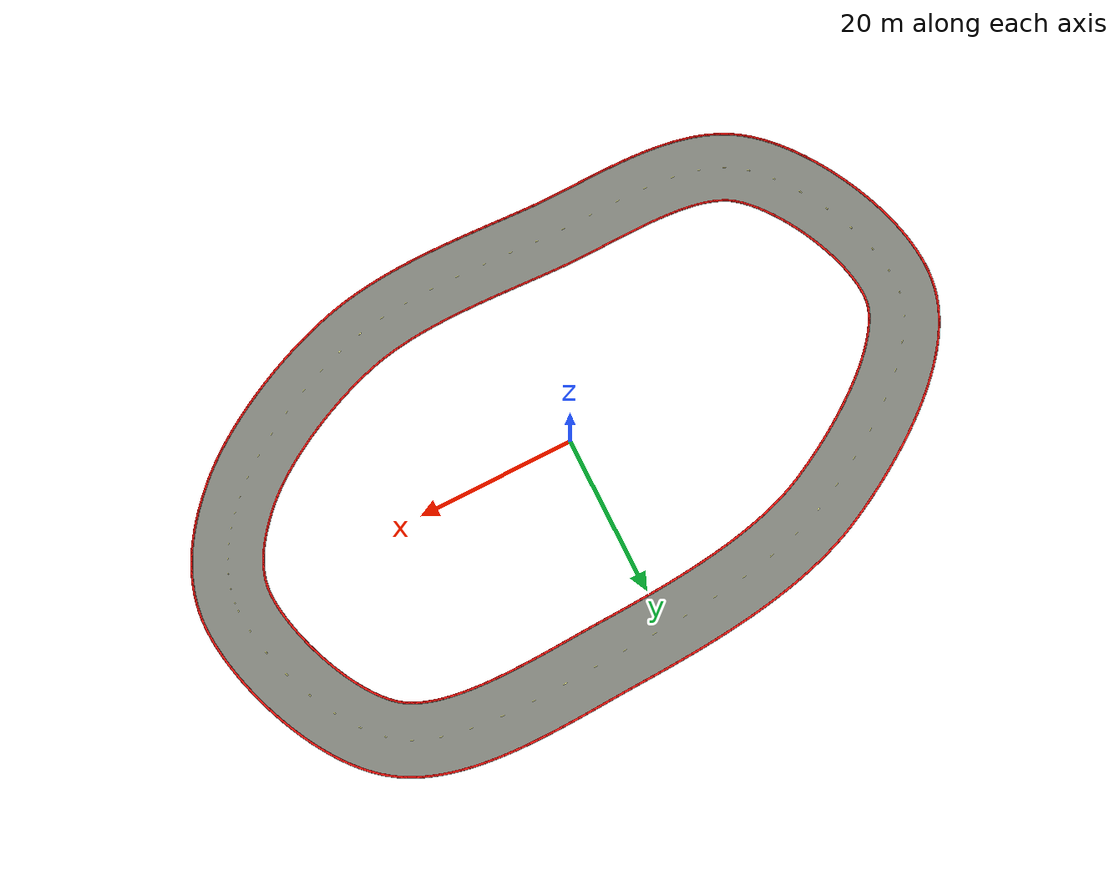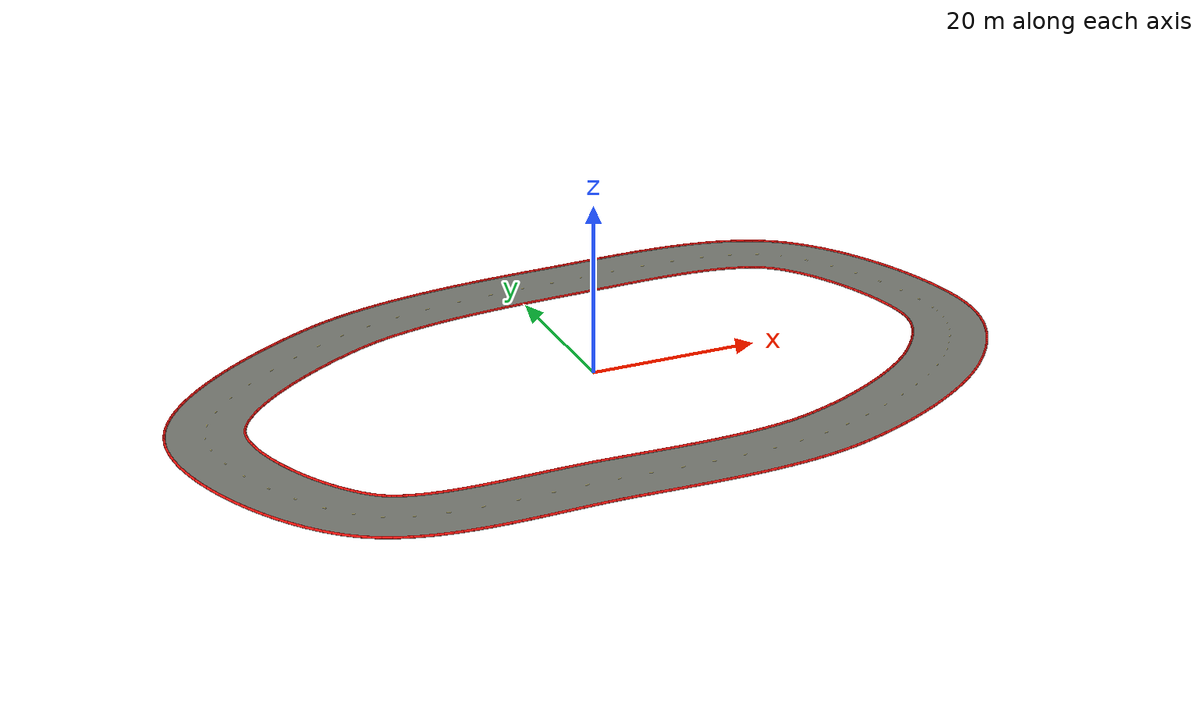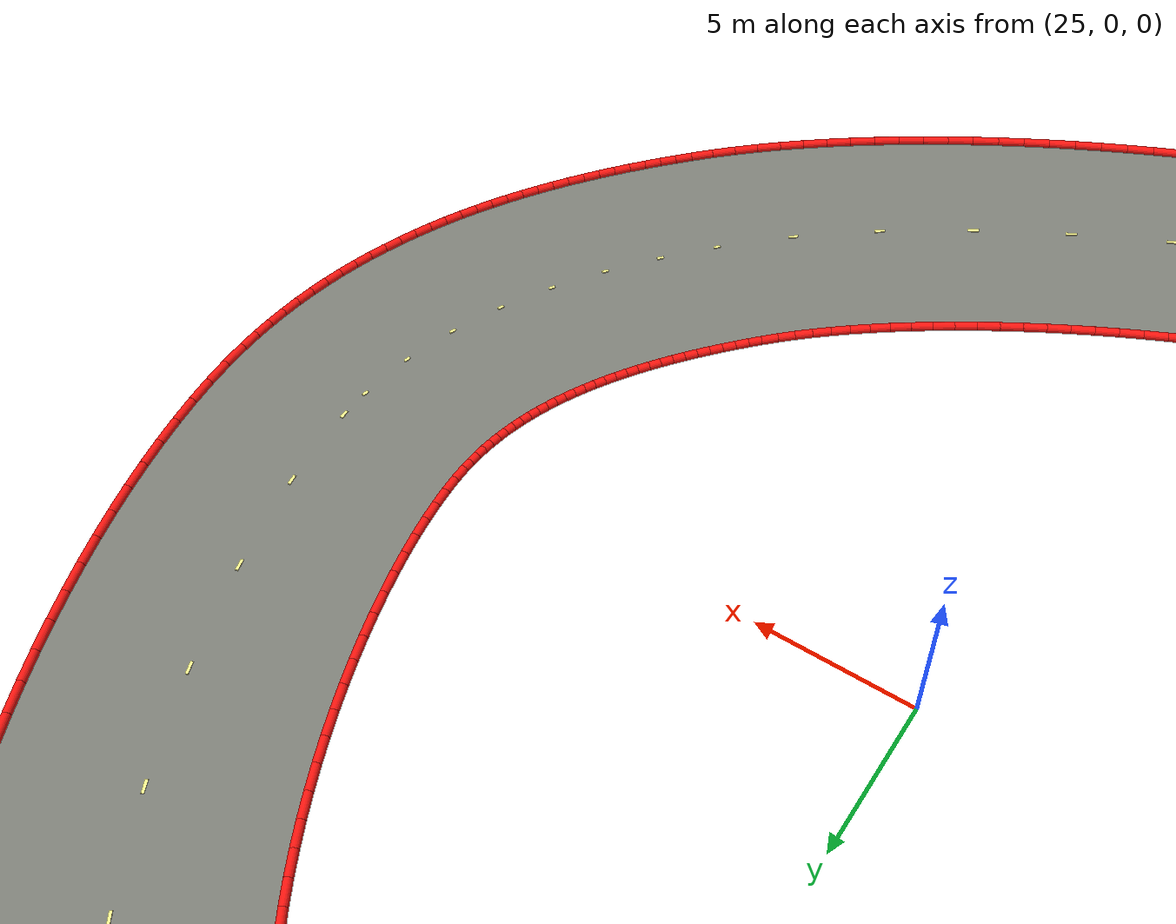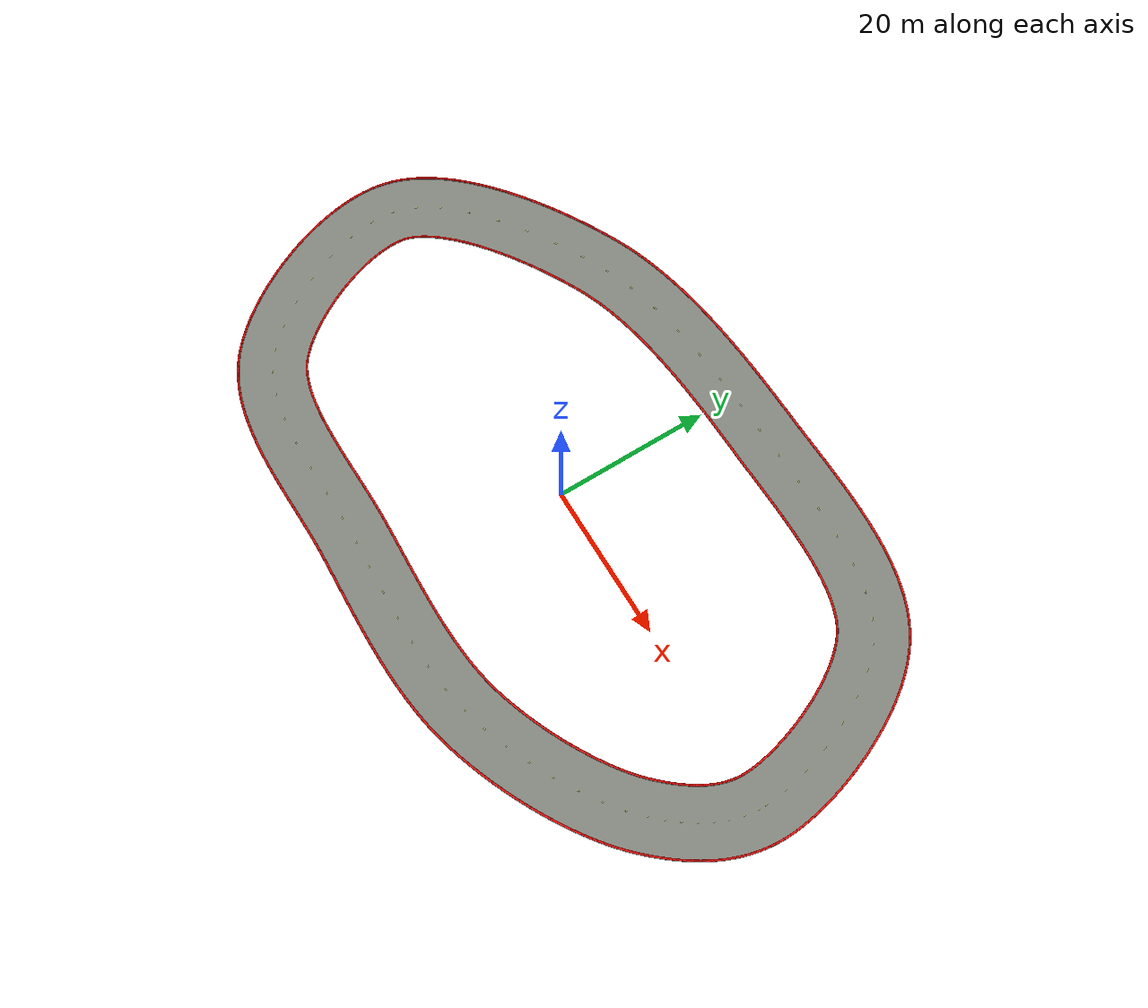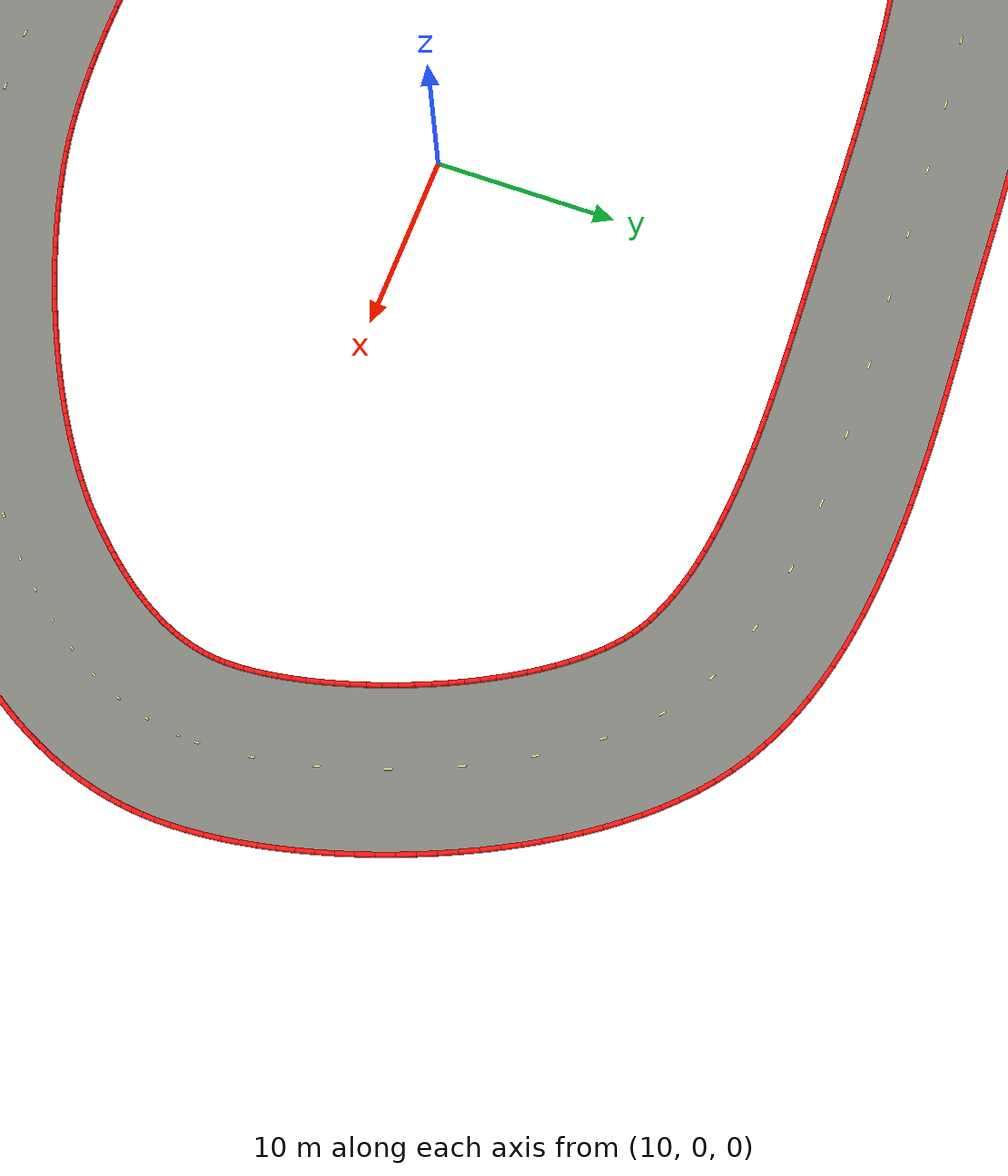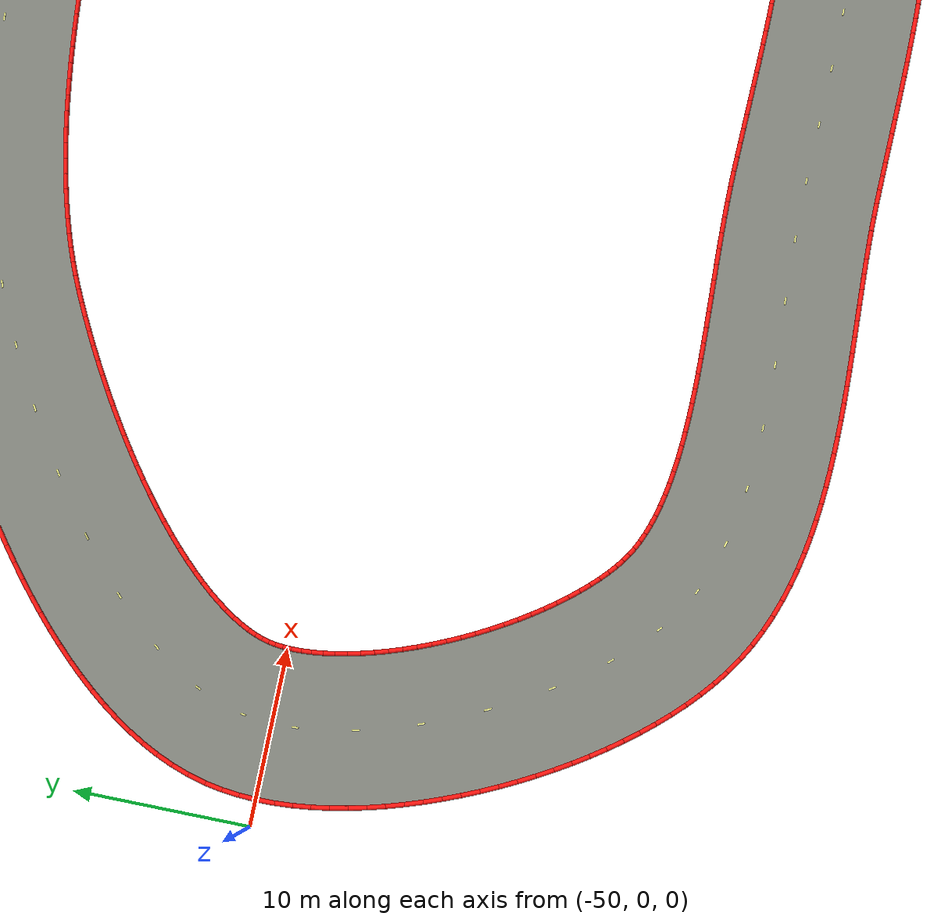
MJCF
<mujoco model="hairpin_track_visuals">
  <asset>
    <mesh name="track_surface_mesh" inertia="shell" vertex="39.75054 0.06778 0.02200 39.74850 0.52960 0.02200 39.72493 1.03173 0.02200 39.67851 1.58154 0.02200 39.60844 2.17278 0.02200 39.51442 2.79986 0.02200 39.39646 3.45773 0.02200 39.25483 4.14173 0.02200 39.08995 4.84754 0.02200 38.90234 5.57104 0.02200 38.69263 6.30834 0.02200 38.46150 7.05567 0.02200 38.20971 7.80936 0.02200 37.93807 8.56586 0.02200 37.64744 9.32163 0.02200 37.33874 10.07322 0.02200 37.01295 10.81718 0.02200 36.67115 11.55009 0.02200 36.31448 12.26854 0.02200 35.94419 12.96913 0.02200 35.56166 13.64844 0.02200 35.16842 14.30307 0.02200 34.76614 14.92964 0.02200 34.35676 15.52475 0.02200 33.94241 16.08510 0.02200 33.52556 16.60745 0.02200 33.10899 17.08870 0.02200 32.69587 17.52600 0.02200 32.28977 17.91688 0.02200 31.89464 18.25940 0.02200 31.51763 18.55032 0.02200 31.09198 18.83614 0.02200 30.63028 19.10402 0.02200 30.12309 19.35887 0.02200 29.57027 19.59932 0.02200 28.97254 19.82402 0.02200 28.33132 20.03176 0.02200 27.64853 20.22160 0.02200 26.92646 20.39290 0.02200 26.16760 20.54535 0.02200 25.37457 20.67891 0.02200 24.55005 20.79383 0.02200 23.69671 20.89055 0.02200 22.81720 20.96975 0.02200 21.91411 21.03223 0.02200 20.98998 21.07895 0.02200 20.04729 21.11097 0.02200 19.08843 21.12944 0.02200 18.11574 21.13558 0.02200 17.13147 21.13068 0.02200 16.13784 21.11606 0.02200 15.13698 21.09311 0.02200 14.13094 21.06322 0.02200 13.12175 21.02783 0.02200 12.11133 20.98841 0.02200 11.10157 20.94643 0.02200 10.09426 20.90341 0.02200 9.09114 20.86086 0.02200 8.09384 20.82035 0.02200 7.10394 20.78345 0.02200 6.13289 20.75208 0.02200 5.14349 20.72213 0.02200 4.15432 20.68966 0.02200 3.15815 20.65373 0.02200 2.15605 20.61367 0.02200 1.14910 20.56883 0.02200 0.13842 20.51854 0.02200 -0.87489 20.46215 0.02200 -1.88968 20.39902 0.02200 -2.90481 20.32850 0.02200 -3.91912 20.24997 0.02200 -4.93143 20.16282 0.02200 -5.94055 20.06643 0.02200 -6.94529 19.96021 0.02200 -7.94443 19.84357 0.02200 -8.93675 19.71594 0.02200 -9.92102 19.57678 0.02200 -10.89600 19.42556 0.02200 -11.86042 19.26177 0.02200 -12.81304 19.08491 0.02200 -13.75259 18.89453 0.02200 -14.67780 18.69021 0.02200 -15.58740 18.47155 0.02200 -16.48012 18.23819 0.02200 -17.35472 17.98980 0.02200 -18.20994 17.72612 0.02200 -19.04458 17.44691 0.02200 -19.85744 17.15199 0.02200 -20.64738 16.84120 0.02200 -21.41333 16.51447 0.02200 -22.17163 16.16339 0.02200 -22.90873 15.80158 0.02200 -23.67727 15.41108 0.02200 -24.45798 15.00066 0.02200 -25.24790 14.57131 0.02200 -26.04412 14.12402 0.02200 -26.84374 13.65980 0.02200 -27.64390 13.17966 0.02200 -28.44175 12.68466 0.02200 -29.23443 12.17587 0.02200 -30.01911 11.65438 0.02200 -30.79293 11.12135 0.02200 -31.55306 10.57797 0.02200 -32.29663 10.02550 0.02200 -33.02079 9.46527 0.02200 -33.72268 8.89870 0.02200 -34.39944 8.32730 0.02200 -35.04820 7.75273 0.02200 -35.66611 7.17677 0.02200 -36.25038 6.60139 0.02200 -36.79825 6.02875 0.02200 -37.30706 5.46126 0.02200 -37.77429 4.90157 0.02200 -38.19766 4.35264 0.02200 -38.57520 3.81770 0.02200 -38.90538 3.30026 0.02200 -39.18729 2.80406 0.02200 -39.42084 2.33288 0.02200 -39.60691 1.89030 0.02200 -39.74757 1.47928 0.02200 -39.84794 1.09287 0.02200 -39.91601 0.70774 0.02200 -39.96342 0.26276 0.02200 -39.98554 -0.23743 0.02200 -39.97909 -0.78757 0.02200 -39.94195 -1.38213 0.02200 -39.87293 -2.01560 0.02200 -39.77156 -2.68265 0.02200 -39.63794 -3.37817 0.02200 -39.47258 -4.09731 0.02200 -39.27630 -4.83544 0.02200 -39.05019 -5.58815 0.02200 -38.79548 -6.35121 0.02200 -38.51357 -7.12057 0.02200 -38.20599 -7.89228 0.02200 -37.87435 -8.66253 0.02200 -37.52035 -9.42756 0.02200 -37.14579 -10.18370 0.02200 -36.75256 -10.92732 0.02200 -36.34264 -11.65484 0.02200 -35.91813 -12.36268 0.02200 -35.48124 -13.04728 0.02200 -35.03435 -13.70510 0.02200 -34.58003 -14.33257 0.02200 -34.12107 -14.92615 0.02200 -33.66055 -15.48229 0.02200 -33.20192 -15.99748 0.02200 -32.74903 -16.46830 0.02200 -32.30632 -16.89147 0.02200 -31.87886 -17.26397 0.02200 -31.48355 -17.57510 0.02200 -31.09624 -17.84166 0.02200 -30.68598 -18.08363 0.02200 -30.23417 -18.31272 0.02200 -29.73967 -18.52799 0.02200 -29.20238 -18.72830 0.02200 -28.62308 -18.91252 0.02200 -28.00325 -19.07973 0.02200 -27.34486 -19.22932 0.02200 -26.65018 -19.36102 0.02200 -25.92168 -19.47488 0.02200 -25.16194 -19.57125 0.02200 -24.37354 -19.65075 0.02200 -23.55906 -19.71424 0.02200 -22.72101 -19.76275 0.02200 -21.86183 -19.79749 0.02200 -20.98390 -19.81979 0.02200 -20.08950 -19.83109 0.02200 -19.18081 -19.83293 0.02200 -18.25994 -19.82689 0.02200 -17.32890 -19.81465 0.02200 -16.38962 -19.79793 0.02200 -15.44393 -19.77848 0.02200 -14.49357 -19.75814 0.02200 -13.54020 -19.73875 0.02200 -12.58536 -19.72221 0.02200 -11.63050 -19.71048 0.02200 -10.67696 -19.70557 0.02200 -9.72595 -19.70958 0.02200 -8.77855 -19.72469 0.02200 -7.85105 -19.75261 0.02200 -6.95619 -19.78833 0.02200 -6.07302 -19.82614 0.02200 -5.18924 -19.86569 0.02200 -4.30532 -19.90618 0.02200 -3.42174 -19.94681 0.02200 -2.53901 -19.98681 0.02200 -1.65765 -20.02538 0.02200 -0.77820 -20.06177 0.02200 0.09879 -20.09521 0.02200 0.97277 -20.12495 0.02200 1.84314 -20.15026 0.02200 2.70934 -20.17039 0.02200 3.57074 -20.18464 0.02200 4.42675 -20.19228 0.02200 5.27674 -20.19263 0.02200 6.12007 -20.18499 0.02200 6.95611 -20.16871 0.02200 7.78419 -20.14314 0.02200 8.60366 -20.10763 0.02200 9.41387 -20.06159 0.02200 10.21414 -20.00441 0.02200 11.00380 -19.93554 0.02200 11.78220 -19.85444 0.02200 12.54868 -19.76060 0.02200 13.30259 -19.65353 0.02200 14.04332 -19.53277 0.02200 14.77025 -19.39792 0.02200 15.48283 -19.24857 0.02200 16.18051 -19.08436 0.02200 16.87332 -18.90206 0.02200 17.53242 -18.71282 0.02200 18.20848 -18.50621 0.02200 18.89090 -18.28524 0.02200 19.57831 -18.05040 0.02200 20.26932 -17.80220 0.02200 20.96261 -17.54116 0.02200 21.65683 -17.26782 0.02200 22.35068 -16.98273 0.02200 23.04287 -16.68645 0.02200 23.73211 -16.37953 0.02200 24.41713 -16.06257 0.02200 25.09666 -15.73615 0.02200 25.76943 -15.40089 0.02200 26.43418 -15.05740 0.02200 27.08965 -14.70631 0.02200 27.73458 -14.34829 0.02200 28.36769 -13.98400 0.02200 28.98773 -13.61416 0.02200 29.59341 -13.23948 0.02200 30.18345 -12.86074 0.02200 30.75656 -12.47872 0.02200 31.31144 -12.09427 0.02200 31.84678 -11.70829 0.02200 32.36125 -11.32174 0.02200 32.85354 -10.93565 0.02200 33.32230 -10.55113 0.02200 33.76620 -10.16942 0.02200 34.18391 -9.79185 0.02200 34.57411 -9.41991 0.02200 34.94982 -9.04046 0.02200 35.23310 -8.74209 0.02200 35.52270 -8.42959 0.02200 35.80461 -8.11720 0.02200 36.07849 -7.80502 0.02200 36.34402 -7.49312 0.02200 36.60091 -7.18160 0.02200 36.84885 -6.87057 0.02200 37.08759 -6.56012 0.02200 37.31687 -6.25037 0.02200 37.53646 -5.94143 0.02200 37.74614 -5.63339 0.02200 37.94574 -5.32637 0.02200 38.13510 -5.02044 0.02200 38.31409 -4.71569 0.02200 38.48262 -4.41217 0.02200 38.64060 -4.10991 0.02200 38.78800 -3.80892 0.02200 38.92480 -3.50916 0.02200 39.05103 -3.21056 0.02200 39.16670 -2.91298 0.02200 39.27186 -2.61623 0.02200 39.36657 -2.32009 0.02200 39.45090 -2.02423 0.02200 39.52488 -1.72828 0.02200 39.58854 -1.43180 0.02200 39.64190 -1.13428 0.02200 39.68491 -0.83514 0.02200 39.71749 -0.53376 0.02200 39.73950 -0.22946 0.02200 48.24946 -0.06778 0.02200 48.24573 0.74649 0.02200 48.20684 1.58595 0.02200 48.13530 2.43762 0.02200 48.03308 3.30213 0.02200 47.90171 4.17947 0.02200 47.74233 5.06909 0.02200 47.55588 5.97001 0.02200 47.34313 6.88098 0.02200 47.10475 7.80048 0.02200 46.84131 8.72681 0.02200 46.55330 9.65813 0.02200 46.24117 10.59248 0.02200 45.90530 11.52782 0.02200 45.54602 12.46207 0.02200 45.16360 13.39309 0.02200 44.75823 14.31869 0.02200 44.33006 15.23670 0.02200 43.87911 16.14492 0.02200 43.40534 17.04114 0.02200 42.90855 17.92317 0.02200 42.38841 18.78879 0.02200 41.84443 19.63579 0.02200 41.27587 20.46194 0.02200 40.68179 21.26495 0.02200 40.06091 22.04245 0.02200 39.41164 22.79191 0.02200 38.73200 23.51058 0.02200 38.01961 24.19533 0.02200 37.27172 24.84249 0.02200 36.48237 25.44968 0.02200 35.59866 26.04307 0.02200 34.67728 26.57876 0.02200 33.73145 27.05495 0.02200 32.76509 27.47607 0.02200 31.78126 27.84656 0.02200 30.78233 28.17071 0.02200 29.77015 28.45256 0.02200 28.74622 28.69583 0.02200 27.71181 28.90390 0.02200 26.66810 29.07991 0.02200 25.61619 29.22670 0.02200 24.55718 29.34689 0.02200 23.49221 29.44290 0.02200 22.42246 29.51702 0.02200 21.34918 29.57136 0.02200 20.27367 29.60796 0.02200 19.19731 29.62874 0.02200 18.12156 29.63558 0.02200 17.04793 29.63027 0.02200 15.97799 29.61456 0.02200 14.91340 29.59017 0.02200 13.85587 29.55877 0.02200 12.80717 29.52201 0.02200 11.76914 29.48152 0.02200 10.74369 29.43889 0.02200 9.73280 29.39572 0.02200 8.73852 29.35354 0.02200 7.76298 29.31391 0.02200 6.80841 29.27831 0.02200 5.86711 29.24792 0.02200 4.87545 29.21790 0.02200 3.86167 29.18462 0.02200 2.83521 29.14759 0.02200 1.79721 29.10610 0.02200 0.74878 29.05940 0.02200 -0.30898 29.00676 0.02200 -1.37498 28.94743 0.02200 -2.44814 28.88065 0.02200 -3.52743 28.80567 0.02200 -4.61178 28.72171 0.02200 -5.70017 28.62799 0.02200 -6.79158 28.52372 0.02200 -7.88501 28.40810 0.02200 -8.97946 28.28031 0.02200 -10.07395 28.13953 0.02200 -11.16751 27.98489 0.02200 -12.25918 27.81554 0.02200 -13.34800 27.63058 0.02200 -14.43302 27.42911 0.02200 -15.51332 27.21017 0.02200 -16.58794 26.97281 0.02200 -17.65597 26.71600 0.02200 -18.71644 26.43873 0.02200 -19.76842 26.13990 0.02200 -20.81095 25.81839 0.02200 -21.84302 25.47304 0.02200 -22.86363 25.10263 0.02200 -23.87172 24.70591 0.02200 -24.86615 24.28158 0.02200 -25.82837 23.83661 0.02200 -26.70591 23.40628 0.02200 -27.58016 22.96207 0.02200 -28.46529 22.49676 0.02200 -29.35918 22.01089 0.02200 -30.25963 21.50504 0.02200 -31.16444 20.97974 0.02200 -32.07140 20.43551 0.02200 -32.97825 19.87286 0.02200 -33.88275 19.29227 0.02200 -34.78265 18.69417 0.02200 -35.67570 18.07898 0.02200 -36.55965 17.44704 0.02200 -37.43226 16.79864 0.02200 -38.29129 16.13399 0.02200 -39.13452 15.45324 0.02200 -39.95971 14.75641 0.02200 -40.76463 14.04339 0.02200 -41.54702 13.31395 0.02200 -42.30460 12.56766 0.02200 -43.03503 11.80392 0.02200 -43.73587 11.02186 0.02200 -44.40454 10.22038 0.02200 -45.03824 9.39808 0.02200 -45.63384 8.55325 0.02200 -46.18778 7.68394 0.02200 -46.69585 6.78797 0.02200 -47.15308 5.86310 0.02200 -47.55347 4.90730 0.02200 -47.88987 3.91914 0.02200 -48.15206 2.90713 0.02200 -48.33061 1.90964 0.02200 -48.43882 0.90898 0.02200 -48.48433 -0.09384 0.02200 -48.47340 -1.09846 0.02200 -48.41118 -2.10476 0.02200 -48.30184 -3.11262 0.02200 -48.14885 -4.12172 0.02200 -47.95513 -5.13155 0.02200 -47.72316 -6.14130 0.02200 -47.45511 -7.14998 0.02200 -47.15292 -8.15635 0.02200 -46.81834 -9.15900 0.02200 -46.45297 -10.15635 0.02200 -46.05830 -11.14671 0.02200 -45.63571 -12.12826 0.02200 -45.18649 -13.09910 0.02200 -44.71186 -14.05727 0.02200 -44.21292 -15.00077 0.02200 -43.69070 -15.92754 0.02200 -43.14611 -16.83552 0.02200 -42.57992 -17.72262 0.02200 -41.99275 -18.58676 0.02200 -41.38506 -19.42587 0.02200 -40.75703 -20.23784 0.02200 -40.10860 -21.02058 0.02200 -39.43933 -21.77197 0.02200 -38.74834 -22.48979 0.02200 -38.03422 -23.17169 0.02200 -37.29489 -23.81504 0.02200 -36.51645 -24.42490 0.02200 -35.66741 -25.00786 0.02200 -34.77411 -25.53595 0.02200 -33.85869 -26.00121 0.02200 -32.92581 -26.40826 0.02200 -31.97911 -26.76197 0.02200 -31.02132 -27.06718 0.02200 -30.05450 -27.32851 0.02200 -29.08021 -27.55029 0.02200 -28.09970 -27.73651 0.02200 -27.11403 -27.89083 0.02200 -26.12415 -28.01661 0.02200 -25.13101 -28.11693 0.02200 -24.13556 -28.19467 0.02200 -23.13880 -28.25248 0.02200 -22.14184 -28.29288 0.02200 -21.14581 -28.31825 0.02200 -20.15198 -28.33087 0.02200 -19.16168 -28.33290 0.02200 -18.17634 -28.32648 0.02200 -17.19746 -28.31363 0.02200 -16.22666 -28.29636 0.02200 -15.26563 -28.27661 0.02200 -14.31615 -28.25629 0.02200 -13.38009 -28.23724 0.02200 -12.45945 -28.22127 0.02200 -11.55629 -28.21015 0.02200 -10.67282 -28.20557 0.02200 -9.81134 -28.20915 0.02200 -8.97431 -28.22243 0.02200 -8.14895 -28.24739 0.02200 -7.30770 -28.28106 0.02200 -6.44483 -28.31800 0.02200 -5.57374 -28.35699 0.02200 -4.69504 -28.39724 0.02200 -3.80933 -28.43797 0.02200 -2.91718 -28.47839 0.02200 -2.01916 -28.51769 0.02200 -1.11581 -28.55506 0.02200 -0.20767 -28.58968 0.02200 0.70474 -28.62073 0.02200 1.62092 -28.64735 0.02200 2.54037 -28.66871 0.02200 3.46261 -28.68395 0.02200 4.38716 -28.69219 0.02200 5.31357 -28.69255 0.02200 6.24139 -28.68413 0.02200 7.17018 -28.66602 0.02200 8.09951 -28.63729 0.02200 9.02894 -28.59699 0.02200 9.95807 -28.54415 0.02200 10.88647 -28.47778 0.02200 11.81372 -28.39687 0.02200 12.73941 -28.30037 0.02200 13.66311 -28.18723 0.02200 14.58438 -28.05632 0.02200 15.50275 -27.90654 0.02200 16.41775 -27.73673 0.02200 17.32887 -27.54569 0.02200 18.23554 -27.33220 0.02200 19.12668 -27.09794 0.02200 19.94684 -26.86270 0.02200 20.75983 -26.61427 0.02200 21.57411 -26.35062 0.02200 22.38895 -26.07226 0.02200 23.20359 -25.77967 0.02200 24.01724 -25.47332 0.02200 24.82911 -25.15367 0.02200 25.63837 -24.82117 0.02200 26.44420 -24.47624 0.02200 27.24574 -24.11932 0.02200 28.04216 -23.75082 0.02200 28.83258 -23.37113 0.02200 29.61615 -22.98065 0.02200 30.39201 -22.57974 0.02200 31.15928 -22.16876 0.02200 31.91710 -21.74805 0.02200 32.66462 -21.31793 0.02200 33.40097 -20.87868 0.02200 34.12531 -20.43058 0.02200 34.83679 -19.97386 0.02200 35.53457 -19.50870 0.02200 36.21783 -19.03526 0.02200 36.88575 -18.55364 0.02200 37.53752 -18.06386 0.02200 38.17236 -17.56590 0.02200 38.78945 -17.05961 0.02200 39.38801 -16.54478 0.02200 39.96725 -16.02105 0.02200 40.52635 -15.48793 0.02200 41.05018 -14.95954 0.02200 41.43156 -14.55836 0.02200 41.79539 -14.16574 0.02200 42.15492 -13.76729 0.02200 42.50976 -13.36278 0.02200 42.85945 -12.95198 0.02200 43.20355 -12.53465 0.02200 43.54159 -12.11054 0.02200 43.87310 -11.67939 0.02200 44.19757 -11.24097 0.02200 44.51448 -10.79500 0.02200 44.82330 -10.34125 0.02200 45.12344 -9.87946 0.02200 45.41432 -9.40940 0.02200 45.69531 -8.93085 0.02200 45.96576 -8.44361 0.02200 46.22498 -7.94750 0.02200 46.47227 -7.44237 0.02200 46.70689 -6.92811 0.02200 46.92807 -6.40465 0.02200 47.13503 -5.87198 0.02200 47.32697 -5.33013 0.02200 47.50308 -4.77921 0.02200 47.66255 -4.21938 0.02200 47.80459 -3.65086 0.02200 47.92840 -3.07396 0.02200 48.03324 -2.48904 0.02200 48.11838 -1.89653 0.02200 48.18317 -1.29690 0.02200 48.22698 -0.69069 0.02200" face="0 271 1 0 270 271 1 272 2 1 271 272 2 273 3 2 272 273 3 274 4 3 273 274 4 275 5 4 274 275 5 276 6 5 275 276 6 277 7 6 276 277 7 278 8 7 277 278 8 279 9 8 278 279 9 280 10 9 279 280 10 281 11 10 280 281 11 282 12 11 281 282 12 283 13 12 282 283 13 284 14 13 283 284 14 285 15 14 284 285 15 286 16 15 285 286 16 287 17 16 286 287 17 288 18 17 287 288 18 289 19 18 288 289 19 290 20 19 289 290 20 291 21 20 290 291 21 292 22 21 291 292 22 293 23 22 292 293 23 294 24 23 293 294 24 295 25 24 294 295 25 296 26 25 295 296 26 297 27 26 296 297 27 298 28 27 297 298 28 299 29 28 298 299 29 300 30 29 299 300 30 301 31 30 300 301 31 302 32 31 301 302 32 303 33 32 302 303 33 304 34 33 303 304 34 305 35 34 304 305 35 306 36 35 305 306 36 307 37 36 306 307 37 308 38 37 307 308 38 309 39 38 308 309 39 310 40 39 309 310 40 311 41 40 310 311 41 312 42 41 311 312 42 313 43 42 312 313 43 314 44 43 313 314 44 315 45 44 314 315 45 316 46 45 315 316 46 317 47 46 316 317 47 318 48 47 317 318 48 319 49 48 318 319 49 320 50 49 319 320 50 321 51 50 320 321 51 322 52 51 321 322 52 323 53 52 322 323 53 324 54 53 323 324 54 325 55 54 324 325 55 326 56 55 325 326 56 327 57 56 326 327 57 328 58 57 327 328 58 329 59 58 328 329 59 330 60 59 329 330 60 331 61 60 330 331 61 332 62 61 331 332 62 333 63 62 332 333 63 334 64 63 333 334 64 335 65 64 334 335 65 336 66 65 335 336 66 337 67 66 336 337 67 338 68 67 337 338 68 339 69 68 338 339 69 340 70 69 339 340 70 341 71 70 340 341 71 342 72 71 341 342 72 343 73 72 342 343 73 344 74 73 343 344 74 345 75 74 344 345 75 346 76 75 345 346 76 347 77 76 346 347 77 348 78 77 347 348 78 349 79 78 348 349 79 350 80 79 349 350 80 351 81 80 350 351 81 352 82 81 351 352 82 353 83 82 352 353 83 354 84 83 353 354 84 355 85 84 354 355 85 356 86 85 355 356 86 357 87 86 356 357 87 358 88 87 357 358 88 359 89 88 358 359 89 360 90 89 359 360 90 361 91 90 360 361 91 362 92 91 361 362 92 363 93 92 362 363 93 364 94 93 363 364 94 365 95 94 364 365 95 366 96 95 365 366 96 367 97 96 366 367 97 368 98 97 367 368 98 369 99 98 368 369 99 370 100 99 369 370 100 371 101 100 370 371 101 372 102 101 371 372 102 373 103 102 372 373 103 374 104 103 373 374 104 375 105 104 374 375 105 376 106 105 375 376 106 377 107 106 376 377 107 378 108 107 377 378 108 379 109 108 378 379 109 380 110 109 379 380 110 381 111 110 380 381 111 382 112 111 381 382 112 383 113 112 382 383 113 384 114 113 383 384 114 385 115 114 384 385 115 386 116 115 385 386 116 387 117 116 386 387 117 388 118 117 387 388 118 389 119 118 388 389 119 390 120 119 389 390 120 391 121 120 390 391 121 392 122 121 391 392 122 393 123 122 392 393 123 394 124 123 393 394 124 395 125 124 394 395 125 396 126 125 395 396 126 397 127 126 396 397 127 398 128 127 397 398 128 399 129 128 398 399 129 400 130 129 399 400 130 401 131 130 400 401 131 402 132 131 401 402 132 403 133 132 402 403 133 404 134 133 403 404 134 405 135 134 404 405 135 406 136 135 405 406 136 407 137 136 406 407 137 408 138 137 407 408 138 409 139 138 408 409 139 410 140 139 409 410 140 411 141 140 410 411 141 412 142 141 411 412 142 413 143 142 412 413 143 414 144 143 413 414 144 415 145 144 414 415 145 416 146 145 415 416 146 417 147 146 416 417 147 418 148 147 417 418 148 419 149 148 418 419 149 420 150 149 419 420 150 421 151 150 420 421 151 422 152 151 421 422 152 423 153 152 422 423 153 424 154 153 423 424 154 425 155 154 424 425 155 426 156 155 425 426 156 427 157 156 426 427 157 428 158 157 427 428 158 429 159 158 428 429 159 430 160 159 429 430 160 431 161 160 430 431 161 432 162 161 431 432 162 433 163 162 432 433 163 434 164 163 433 434 164 435 165 164 434 435 165 436 166 165 435 436 166 437 167 166 436 437 167 438 168 167 437 438 168 439 169 168 438 439 169 440 170 169 439 440 170 441 171 170 440 441 171 442 172 171 441 442 172 443 173 172 442 443 173 444 174 173 443 444 174 445 175 174 444 445 175 446 176 175 445 446 176 447 177 176 446 447 177 448 178 177 447 448 178 449 179 178 448 449 179 450 180 179 449 450 180 451 181 180 450 451 181 452 182 181 451 452 182 453 183 182 452 453 183 454 184 183 453 454 184 455 185 184 454 455 185 456 186 185 455 456 186 457 187 186 456 457 187 458 188 187 457 458 188 459 189 188 458 459 189 460 190 189 459 460 190 461 191 190 460 461 191 462 192 191 461 462 192 463 193 192 462 463 193 464 194 193 463 464 194 465 195 194 464 465 195 466 196 195 465 466 196 467 197 196 466 467 197 468 198 197 467 468 198 469 199 198 468 469 199 470 200 199 469 470 200 471 201 200 470 471 201 472 202 201 471 472 202 473 203 202 472 473 203 474 204 203 473 474 204 475 205 204 474 475 205 476 206 205 475 476 206 477 207 206 476 477 207 478 208 207 477 478 208 479 209 208 478 479 209 480 210 209 479 480 210 481 211 210 480 481 211 482 212 211 481 482 212 483 213 212 482 483 213 484 214 213 483 484 214 485 215 214 484 485 215 486 216 215 485 486 216 487 217 216 486 487 217 488 218 217 487 488 218 489 219 218 488 489 219 490 220 219 489 490 220 491 221 220 490 491 221 492 222 221 491 492 222 493 223 222 492 493 223 494 224 223 493 494 224 495 225 224 494 495 225 496 226 225 495 496 226 497 227 226 496 497 227 498 228 227 497 498 228 499 229 228 498 499 229 500 230 229 499 500 230 501 231 230 500 501 231 502 232 231 501 502 232 503 233 232 502 503 233 504 234 233 503 504 234 505 235 234 504 505 235 506 236 235 505 506 236 507 237 236 506 507 237 508 238 237 507 508 238 509 239 238 508 509 239 510 240 239 509 510 240 511 241 240 510 511 241 512 242 241 511 512 242 513 243 242 512 513 243 514 244 243 513 514 244 515 245 244 514 515 245 516 246 245 515 516 246 517 247 246 516 517 247 518 248 247 517 518 248 519 249 248 518 519 249 520 250 249 519 520 250 521 251 250 520 521 251 522 252 251 521 522 252 523 253 252 522 523 253 524 254 253 523 524 254 525 255 254 524 525 255 526 256 255 525 526 256 527 257 256 526 527 257 528 258 257 527 528 258 529 259 258 528 529 259 530 260 259 529 530 260 531 261 260 530 531 261 532 262 261 531 532 262 533 263 262 532 533 263 534 264 263 533 534 264 535 265 264 534 535 265 536 266 265 535 536 266 537 267 266 536 537 267 538 268 267 537 538 268 539 269 268 538 539 269 270 0 269 539 270"/>
    <material name="track_asphalt" rgba="0.48 0.49 0.46 1" emission="0.08"/>
    <material name="track_boundary" rgba="0.95 0.08 0.06 1" emission="0.05"/>
    <material name="track_centerline" rgba="1.0 0.95 0.55 1" emission="0.15"/>
  </asset>
  <worldbody>
    <geom name="track_surface" type="mesh" mesh="track_surface_mesh" material="track_asphalt" contype="0" conaffinity="0"/>
    <geom name="track_left_boundary_000" type="capsule" fromto="39.75054 0.06778 0.09 39.74850 0.52960 0.09" size="0.14" material="track_boundary" contype="0" conaffinity="0"/>
    <geom name="track_left_boundary_001" type="capsule" fromto="39.74850 0.52960 0.09 39.72493 1.03173 0.09" size="0.14" material="track_boundary" contype="0" conaffinity="0"/>
    <geom name="track_left_boundary_002" type="capsule" fromto="39.72493 1.03173 0.09 39.67851 1.58154 0.09" size="0.14" material="track_boundary" contype="0" conaffinity="0"/>
    <geom name="track_left_boundary_003" type="capsule" fromto="39.67851 1.58154 0.09 39.60844 2.17278 0.09" size="0.14" material="track_boundary" contype="0" conaffinity="0"/>
    <geom name="track_left_boundary_004" type="capsule" fromto="39.60844 2.17278 0.09 39.51442 2.79986 0.09" size="0.14" material="track_boundary" contype="0" conaffinity="0"/>
    <geom name="track_left_boundary_005" type="capsule" fromto="39.51442 2.79986 0.09 39.39646 3.45773 0.09" size="0.14" material="track_boundary" contype="0" conaffinity="0"/>
    <geom name="track_left_boundary_006" type="capsule" fromto="39.39646 3.45773 0.09 39.25483 4.14173 0.09" size="0.14" material="track_boundary" contype="0" conaffinity="0"/>
    <geom name="track_left_boundary_007" type="capsule" fromto="39.25483 4.14173 0.09 39.08995 4.84754 0.09" size="0.14" material="track_boundary" contype="0" conaffinity="0"/>
    <geom name="track_left_boundary_008" type="capsule" fromto="39.08995 4.84754 0.09 38.90234 5.57104 0.09" size="0.14" material="track_boundary" contype="0" conaffinity="0"/>
    <geom name="track_left_boundary_009" type="capsule" fromto="38.90234 5.57104 0.09 38.69263 6.30834 0.09" size="0.14" material="track_boundary" contype="0" conaffinity="0"/>
    <geom name="track_left_boundary_010" type="capsule" fromto="38.69263 6.30834 0.09 38.46150 7.05567 0.09" size="0.14" material="track_boundary" contype="0" conaffinity="0"/>
    <geom name="track_left_boundary_011" type="capsule" fromto="38.46150 7.05567 0.09 38.20971 7.80936 0.09" size="0.14" material="track_boundary" contype="0" conaffinity="0"/>
    <geom name="track_left_boundary_012" type="capsule" fromto="38.20971 7.80936 0.09 37.93807 8.56586 0.09" size="0.14" material="track_boundary" contype="0" conaffinity="0"/>
    <geom name="track_left_boundary_013" type="capsule" fromto="37.93807 8.56586 0.09 37.64744 9.32163 0.09" size="0.14" material="track_boundary" contype="0" conaffinity="0"/>
    <geom name="track_left_boundary_014" type="capsule" fromto="37.64744 9.32163 0.09 37.33874 10.07322 0.09" size="0.14" material="track_boundary" contype="0" conaffinity="0"/>
    <geom name="track_left_boundary_015" type="capsule" fromto="37.33874 10.07322 0.09 37.01295 10.81718 0.09" size="0.14" material="track_boundary" contype="0" conaffinity="0"/>
    <geom name="track_left_boundary_016" type="capsule" fromto="37.01295 10.81718 0.09 36.67115 11.55009 0.09" size="0.14" material="track_boundary" contype="0" conaffinity="0"/>
    <geom name="track_left_boundary_017" type="capsule" fromto="36.67115 11.55009 0.09 36.31448 12.26854 0.09" size="0.14" material="track_boundary" contype="0" conaffinity="0"/>
    <geom name="track_left_boundary_018" type="capsule" fromto="36.31448 12.26854 0.09 35.94419 12.96913 0.09" size="0.14" material="track_boundary" contype="0" conaffinity="0"/>
    <geom name="track_left_boundary_019" type="capsule" fromto="35.94419 12.96913 0.09 35.56166 13.64844 0.09" size="0.14" material="track_boundary" contype="0" conaffinity="0"/>
    <geom name="track_left_boundary_020" type="capsule" fromto="35.56166 13.64844 0.09 35.16842 14.30307 0.09" size="0.14" material="track_boundary" contype="0" conaffinity="0"/>
    <geom name="track_left_boundary_021" type="capsule" fromto="35.16842 14.30307 0.09 34.76614 14.92964 0.09" size="0.14" material="track_boundary" contype="0" conaffinity="0"/>
    <geom name="track_left_boundary_022" type="capsule" fromto="34.76614 14.92964 0.09 34.35676 15.52475 0.09" size="0.14" material="track_boundary" contype="0" conaffinity="0"/>
    <geom name="track_left_boundary_023" type="capsule" fromto="34.35676 15.52475 0.09 33.94241 16.08510 0.09" size="0.14" material="track_boundary" contype="0" conaffinity="0"/>
    <geom name="track_left_boundary_024" type="capsule" fromto="33.94241 16.08510 0.09 33.52556 16.60745 0.09" size="0.14" material="track_boundary" contype="0" conaffinity="0"/>
    <geom name="track_left_boundary_025" type="capsule" fromto="33.52556 16.60745 0.09 33.10899 17.08870 0.09" size="0.14" material="track_boundary" contype="0" conaffinity="0"/>
    <geom name="track_left_boundary_026" type="capsule" fromto="33.10899 17.08870 0.09 32.69587 17.52600 0.09" size="0.14" material="track_boundary" contype="0" conaffinity="0"/>
    <geom name="track_left_boundary_027" type="capsule" fromto="32.69587 17.52600 0.09 32.28977 17.91688 0.09" size="0.14" material="track_boundary" contype="0" conaffinity="0"/>
    <geom name="track_left_boundary_028" type="capsule" fromto="32.28977 17.91688 0.09 31.89464 18.25940 0.09" size="0.14" material="track_boundary" contype="0" conaffinity="0"/>
    <geom name="track_left_boundary_029" type="capsule" fromto="31.89464 18.25940 0.09 31.51763 18.55032 0.09" size="0.14" material="track_boundary" contype="0" conaffinity="0"/>
    <geom name="track_left_boundary_030" type="capsule" fromto="31.51763 18.55032 0.09 31.09198 18.83614 0.09" size="0.14" material="track_boundary" contype="0" conaffinity="0"/>
    <geom name="track_left_boundary_031" type="capsule" fromto="31.09198 18.83614 0.09 30.63028 19.10402 0.09" size="0.14" material="track_boundary" contype="0" conaffinity="0"/>
    <geom name="track_left_boundary_032" type="capsule" fromto="30.63028 19.10402 0.09 30.12309 19.35887 0.09" size="0.14" material="track_boundary" contype="0" conaffinity="0"/>
    <geom name="track_left_boundary_033" type="capsule" fromto="30.12309 19.35887 0.09 29.57027 19.59932 0.09" size="0.14" material="track_boundary" contype="0" conaffinity="0"/>
    <geom name="track_left_boundary_034" type="capsule" fromto="29.57027 19.59932 0.09 28.97254 19.82402 0.09" size="0.14" material="track_boundary" contype="0" conaffinity="0"/>
    <geom name="track_left_boundary_035" type="capsule" fromto="28.97254 19.82402 0.09 28.33132 20.03176 0.09" size="0.14" material="track_boundary" contype="0" conaffinity="0"/>
    <geom name="track_left_boundary_036" type="capsule" fromto="28.33132 20.03176 0.09 27.64853 20.22160 0.09" size="0.14" material="track_boundary" contype="0" conaffinity="0"/>
    <geom name="track_left_boundary_037" type="capsule" fromto="27.64853 20.22160 0.09 26.92646 20.39290 0.09" size="0.14" material="track_boundary" contype="0" conaffinity="0"/>
    <geom name="track_left_boundary_038" type="capsule" fromto="26.92646 20.39290 0.09 26.16760 20.54535 0.09" size="0.14" material="track_boundary" contype="0" conaffinity="0"/>
    <geom name="track_left_boundary_039" type="capsule" fromto="26.16760 20.54535 0.09 25.37457 20.67891 0.09" size="0.14" material="track_boundary" contype="0" conaffinity="0"/>
    <geom name="track_left_boundary_040" type="capsule" fromto="25.37457 20.67891 0.09 24.55005 20.79383 0.09" size="0.14" material="track_boundary" contype="0" conaffinity="0"/>
    <geom name="track_left_boundary_041" type="capsule" fromto="24.55005 20.79383 0.09 23.69671 20.89055 0.09" size="0.14" material="track_boundary" contype="0" conaffinity="0"/>
    <geom name="track_left_boundary_042" type="capsule" fromto="23.69671 20.89055 0.09 22.81720 20.96975 0.09" size="0.14" material="track_boundary" contype="0" conaffinity="0"/>
    <geom name="track_left_boundary_043" type="capsule" fromto="22.81720 20.96975 0.09 21.91411 21.03223 0.09" size="0.14" material="track_boundary" contype="0" conaffinity="0"/>
    <geom name="track_left_boundary_044" type="capsule" fromto="21.91411 21.03223 0.09 20.98998 21.07895 0.09" size="0.14" material="track_boundary" contype="0" conaffinity="0"/>
    <geom name="track_left_boundary_045" type="capsule" fromto="20.98998 21.07895 0.09 20.04729 21.11097 0.09" size="0.14" material="track_boundary" contype="0" conaffinity="0"/>
    <geom name="track_left_boundary_046" type="capsule" fromto="20.04729 21.11097 0.09 19.08843 21.12944 0.09" size="0.14" material="track_boundary" contype="0" conaffinity="0"/>
    <geom name="track_left_boundary_047" type="capsule" fromto="19.08843 21.12944 0.09 18.11574 21.13558 0.09" size="0.14" material="track_boundary" contype="0" conaffinity="0"/>
    <geom name="track_left_boundary_048" type="capsule" fromto="18.11574 21.13558 0.09 17.13147 21.13068 0.09" size="0.14" material="track_boundary" contype="0" conaffinity="0"/>
    <geom name="track_left_boundary_049" type="capsule" fromto="17.13147 21.13068 0.09 16.13784 21.11606 0.09" size="0.14" material="track_boundary" contype="0" conaffinity="0"/>
    <geom name="track_left_boundary_050" type="capsule" fromto="16.13784 21.11606 0.09 15.13698 21.09311 0.09" size="0.14" material="track_boundary" contype="0" conaffinity="0"/>
    <geom name="track_left_boundary_051" type="capsule" fromto="15.13698 21.09311 0.09 14.13094 21.06322 0.09" size="0.14" material="track_boundary" contype="0" conaffinity="0"/>
    <geom name="track_left_boundary_052" type="capsule" fromto="14.13094 21.06322 0.09 13.12175 21.02783 0.09" size="0.14" material="track_boundary" contype="0" conaffinity="0"/>
    <geom name="track_left_boundary_053" type="capsule" fromto="13.12175 21.02783 0.09 12.11133 20.98841 0.09" size="0.14" material="track_boundary" contype="0" conaffinity="0"/>
    <geom name="track_left_boundary_054" type="capsule" fromto="12.11133 20.98841 0.09 11.10157 20.94643 0.09" size="0.14" material="track_boundary" contype="0" conaffinity="0"/>
    <geom name="track_left_boundary_055" type="capsule" fromto="11.10157 20.94643 0.09 10.09426 20.90341 0.09" size="0.14" material="track_boundary" contype="0" conaffinity="0"/>
    <geom name="track_left_boundary_056" type="capsule" fromto="10.09426 20.90341 0.09 9.09114 20.86086 0.09" size="0.14" material="track_boundary" contype="0" conaffinity="0"/>
    <geom name="track_left_boundary_057" type="capsule" fromto="9.09114 20.86086 0.09 8.09384 20.82035 0.09" size="0.14" material="track_boundary" contype="0" conaffinity="0"/>
    <geom name="track_left_boundary_058" type="capsule" fromto="8.09384 20.82035 0.09 7.10394 20.78345 0.09" size="0.14" material="track_boundary" contype="0" conaffinity="0"/>
    <geom name="track_left_boundary_059" type="capsule" fromto="7.10394 20.78345 0.09 6.13289 20.75208 0.09" size="0.14" material="track_boundary" contype="0" conaffinity="0"/>
    <geom name="track_left_boundary_060" type="capsule" fromto="6.13289 20.75208 0.09 5.14349 20.72213 0.09" size="0.14" material="track_boundary" contype="0" conaffinity="0"/>
    <geom name="track_left_boundary_061" type="capsule" fromto="5.14349 20.72213 0.09 4.15432 20.68966 0.09" size="0.14" material="track_boundary" contype="0" conaffinity="0"/>
    <geom name="track_left_boundary_062" type="capsule" fromto="4.15432 20.68966 0.09 3.15815 20.65373 0.09" size="0.14" material="track_boundary" contype="0" conaffinity="0"/>
    <geom name="track_left_boundary_063" type="capsule" fromto="3.15815 20.65373 0.09 2.15605 20.61367 0.09" size="0.14" material="track_boundary" contype="0" conaffinity="0"/>
    <geom name="track_left_boundary_064" type="capsule" fromto="2.15605 20.61367 0.09 1.14910 20.56883 0.09" size="0.14" material="track_boundary" contype="0" conaffinity="0"/>
    <geom name="track_left_boundary_065" type="capsule" fromto="1.14910 20.56883 0.09 0.13842 20.51854 0.09" size="0.14" material="track_boundary" contype="0" conaffinity="0"/>
    <geom name="track_left_boundary_066" type="capsule" fromto="0.13842 20.51854 0.09 -0.87489 20.46215 0.09" size="0.14" material="track_boundary" contype="0" conaffinity="0"/>
    <geom name="track_left_boundary_067" type="capsule" fromto="-0.87489 20.46215 0.09 -1.88968 20.39902 0.09" size="0.14" material="track_boundary" contype="0" conaffinity="0"/>
    <geom name="track_left_boundary_068" type="capsule" fromto="-1.88968 20.39902 0.09 -2.90481 20.32850 0.09" size="0.14" material="track_boundary" contype="0" conaffinity="0"/>
    <geom name="track_left_boundary_069" type="capsule" fromto="-2.90481 20.32850 0.09 -3.91912 20.24997 0.09" size="0.14" material="track_boundary" contype="0" conaffinity="0"/>
    <geom name="track_left_boundary_070" type="capsule" fromto="-3.91912 20.24997 0.09 -4.93143 20.16282 0.09" size="0.14" material="track_boundary" contype="0" conaffinity="0"/>
    <geom name="track_left_boundary_071" type="capsule" fromto="-4.93143 20.16282 0.09 -5.94055 20.06643 0.09" size="0.14" material="track_boundary" contype="0" conaffinity="0"/>
    <geom name="track_left_boundary_072" type="capsule" fromto="-5.94055 20.06643 0.09 -6.94529 19.96021 0.09" size="0.14" material="track_boundary" contype="0" conaffinity="0"/>
    <geom name="track_left_boundary_073" type="capsule" fromto="-6.94529 19.96021 0.09 -7.94443 19.84357 0.09" size="0.14" material="track_boundary" contype="0" conaffinity="0"/>
    <geom name="track_left_boundary_074" type="capsule" fromto="-7.94443 19.84357 0.09 -8.93675 19.71594 0.09" size="0.14" material="track_boundary" contype="0" conaffinity="0"/>
    <geom name="track_left_boundary_075" type="capsule" fromto="-8.93675 19.71594 0.09 -9.92102 19.57678 0.09" size="0.14" material="track_boundary" contype="0" conaffinity="0"/>
    <geom name="track_left_boundary_076" type="capsule" fromto="-9.92102 19.57678 0.09 -10.89600 19.42556 0.09" size="0.14" material="track_boundary" contype="0" conaffinity="0"/>
    <geom name="track_left_boundary_077" type="capsule" fromto="-10.89600 19.42556 0.09 -11.86042 19.26177 0.09" size="0.14" material="track_boundary" contype="0" conaffinity="0"/>
    <geom name="track_left_boundary_078" type="capsule" fromto="-11.86042 19.26177 0.09 -12.81304 19.08491 0.09" size="0.14" material="track_boundary" contype="0" conaffinity="0"/>
    <geom name="track_left_boundary_079" type="capsule" fromto="-12.81304 19.08491 0.09 -13.75259 18.89453 0.09" size="0.14" material="track_boundary" contype="0" conaffinity="0"/>
    <geom name="track_left_boundary_080" type="capsule" fromto="-13.75259 18.89453 0.09 -14.67780 18.69021 0.09" size="0.14" material="track_boundary" contype="0" conaffinity="0"/>
    <geom name="track_left_boundary_081" type="capsule" fromto="-14.67780 18.69021 0.09 -15.58740 18.47155 0.09" size="0.14" material="track_boundary" contype="0" conaffinity="0"/>
    <geom name="track_left_boundary_082" type="capsule" fromto="-15.58740 18.47155 0.09 -16.48012 18.23819 0.09" size="0.14" material="track_boundary" contype="0" conaffinity="0"/>
    <geom name="track_left_boundary_083" type="capsule" fromto="-16.48012 18.23819 0.09 -17.35472 17.98980 0.09" size="0.14" material="track_boundary" contype="0" conaffinity="0"/>
    <geom name="track_left_boundary_084" type="capsule" fromto="-17.35472 17.98980 0.09 -18.20994 17.72612 0.09" size="0.14" material="track_boundary" contype="0" conaffinity="0"/>
    <geom name="track_left_boundary_085" type="capsule" fromto="-18.20994 17.72612 0.09 -19.04458 17.44691 0.09" size="0.14" material="track_boundary" contype="0" conaffinity="0"/>
    <geom name="track_left_boundary_086" type="capsule" fromto="-19.04458 17.44691 0.09 -19.85744 17.15199 0.09" size="0.14" material="track_boundary" contype="0" conaffinity="0"/>
    <geom name="track_left_boundary_087" type="capsule" fromto="-19.85744 17.15199 0.09 -20.64738 16.84120 0.09" size="0.14" material="track_boundary" contype="0" conaffinity="0"/>
    <geom name="track_left_boundary_088" type="capsule" fromto="-20.64738 16.84120 0.09 -21.41333 16.51447 0.09" size="0.14" material="track_boundary" contype="0" conaffinity="0"/>
    <geom name="track_left_boundary_089" type="capsule" fromto="-21.41333 16.51447 0.09 -22.17163 16.16339 0.09" size="0.14" material="track_boundary" contype="0" conaffinity="0"/>
    <geom name="track_left_boundary_090" type="capsule" fromto="-22.17163 16.16339 0.09 -22.90873 15.80158 0.09" size="0.14" material="track_boundary" contype="0" conaffinity="0"/>
    <geom name="track_left_boundary_091" type="capsule" fromto="-22.90873 15.80158 0.09 -23.67727 15.41108 0.09" size="0.14" material="track_boundary" contype="0" conaffinity="0"/>
    <geom name="track_left_boundary_092" type="capsule" fromto="-23.67727 15.41108 0.09 -24.45798 15.00066 0.09" size="0.14" material="track_boundary" contype="0" conaffinity="0"/>
    <geom name="track_left_boundary_093" type="capsule" fromto="-24.45798 15.00066 0.09 -25.24790 14.57131 0.09" size="0.14" material="track_boundary" contype="0" conaffinity="0"/>
    <geom name="track_left_boundary_094" type="capsule" fromto="-25.24790 14.57131 0.09 -26.04412 14.12402 0.09" size="0.14" material="track_boundary" contype="0" conaffinity="0"/>
    <geom name="track_left_boundary_095" type="capsule" fromto="-26.04412 14.12402 0.09 -26.84374 13.65980 0.09" size="0.14" material="track_boundary" contype="0" conaffinity="0"/>
    <geom name="track_left_boundary_096" type="capsule" fromto="-26.84374 13.65980 0.09 -27.64390 13.17966 0.09" size="0.14" material="track_boundary" contype="0" conaffinity="0"/>
    <geom name="track_left_boundary_097" type="capsule" fromto="-27.64390 13.17966 0.09 -28.44175 12.68466 0.09" size="0.14" material="track_boundary" contype="0" conaffinity="0"/>
    <geom name="track_left_boundary_098" type="capsule" fromto="-28.44175 12.68466 0.09 -29.23443 12.17587 0.09" size="0.14" material="track_boundary" contype="0" conaffinity="0"/>
    <geom name="track_left_boundary_099" type="capsule" fromto="-29.23443 12.17587 0.09 -30.01911 11.65438 0.09" size="0.14" material="track_boundary" contype="0" conaffinity="0"/>
    <geom name="track_left_boundary_100" type="capsule" fromto="-30.01911 11.65438 0.09 -30.79293 11.12135 0.09" size="0.14" material="track_boundary" contype="0" conaffinity="0"/>
    <geom name="track_left_boundary_101" type="capsule" fromto="-30.79293 11.12135 0.09 -31.55306 10.57797 0.09" size="0.14" material="track_boundary" contype="0" conaffinity="0"/>
    <geom name="track_left_boundary_102" type="capsule" fromto="-31.55306 10.57797 0.09 -32.29663 10.02550 0.09" size="0.14" material="track_boundary" contype="0" conaffinity="0"/>
    <geom name="track_left_boundary_103" type="capsule" fromto="-32.29663 10.02550 0.09 -33.02079 9.46527 0.09" size="0.14" material="track_boundary" contype="0" conaffinity="0"/>
    <geom name="track_left_boundary_104" type="capsule" fromto="-33.02079 9.46527 0.09 -33.72268 8.89870 0.09" size="0.14" material="track_boundary" contype="0" conaffinity="0"/>
    <geom name="track_left_boundary_105" type="capsule" fromto="-33.72268 8.89870 0.09 -34.39944 8.32730 0.09" size="0.14" material="track_boundary" contype="0" conaffinity="0"/>
    <geom name="track_left_boundary_106" type="capsule" fromto="-34.39944 8.32730 0.09 -35.04820 7.75273 0.09" size="0.14" material="track_boundary" contype="0" conaffinity="0"/>
    <geom name="track_left_boundary_107" type="capsule" fromto="-35.04820 7.75273 0.09 -35.66611 7.17677 0.09" size="0.14" material="track_boundary" contype="0" conaffinity="0"/>
    <geom name="track_left_boundary_108" type="capsule" fromto="-35.66611 7.17677 0.09 -36.25038 6.60139 0.09" size="0.14" material="track_boundary" contype="0" conaffinity="0"/>
    <geom name="track_left_boundary_109" type="capsule" fromto="-36.25038 6.60139 0.09 -36.79825 6.02875 0.09" size="0.14" material="track_boundary" contype="0" conaffinity="0"/>
    <geom name="track_left_boundary_110" type="capsule" fromto="-36.79825 6.02875 0.09 -37.30706 5.46126 0.09" size="0.14" material="track_boundary" contype="0" conaffinity="0"/>
    <geom name="track_left_boundary_111" type="capsule" fromto="-37.30706 5.46126 0.09 -37.77429 4.90157 0.09" size="0.14" material="track_boundary" contype="0" conaffinity="0"/>
    <geom name="track_left_boundary_112" type="capsule" fromto="-37.77429 4.90157 0.09 -38.19766 4.35264 0.09" size="0.14" material="track_boundary" contype="0" conaffinity="0"/>
    <geom name="track_left_boundary_113" type="capsule" fromto="-38.19766 4.35264 0.09 -38.57520 3.81770 0.09" size="0.14" material="track_boundary" contype="0" conaffinity="0"/>
    <geom name="track_left_boundary_114" type="capsule" fromto="-38.57520 3.81770 0.09 -38.90538 3.30026 0.09" size="0.14" material="track_boundary" contype="0" conaffinity="0"/>
    <geom name="track_left_boundary_115" type="capsule" fromto="-38.90538 3.30026 0.09 -39.18729 2.80406 0.09" size="0.14" material="track_boundary" contype="0" conaffinity="0"/>
    <geom name="track_left_boundary_116" type="capsule" fromto="-39.18729 2.80406 0.09 -39.42084 2.33288 0.09" size="0.14" material="track_boundary" contype="0" conaffinity="0"/>
    <geom name="track_left_boundary_117" type="capsule" fromto="-39.42084 2.33288 0.09 -39.60691 1.89030 0.09" size="0.14" material="track_boundary" contype="0" conaffinity="0"/>
    <geom name="track_left_boundary_118" type="capsule" fromto="-39.60691 1.89030 0.09 -39.74757 1.47928 0.09" size="0.14" material="track_boundary" contype="0" conaffinity="0"/>
    <geom name="track_left_boundary_119" type="capsule" fromto="-39.74757 1.47928 0.09 -39.84794 1.09287 0.09" size="0.14" material="track_boundary" contype="0" conaffinity="0"/>
    <geom name="track_left_boundary_120" type="capsule" fromto="-39.84794 1.09287 0.09 -39.91601 0.70774 0.09" size="0.14" material="track_boundary" contype="0" conaffinity="0"/>
    <geom name="track_left_boundary_121" type="capsule" fromto="-39.91601 0.70774 0.09 -39.96342 0.26276 0.09" size="0.14" material="track_boundary" contype="0" conaffinity="0"/>
    <geom name="track_left_boundary_122" type="capsule" fromto="-39.96342 0.26276 0.09 -39.98554 -0.23743 0.09" size="0.14" material="track_boundary" contype="0" conaffinity="0"/>
    <geom name="track_left_boundary_123" type="capsule" fromto="-39.98554 -0.23743 0.09 -39.97909 -0.78757 0.09" size="0.14" material="track_boundary" contype="0" conaffinity="0"/>
    <geom name="track_left_boundary_124" type="capsule" fromto="-39.97909 -0.78757 0.09 -39.94195 -1.38213 0.09" size="0.14" material="track_boundary" contype="0" conaffinity="0"/>
    <geom name="track_left_boundary_125" type="capsule" fromto="-39.94195 -1.38213 0.09 -39.87293 -2.01560 0.09" size="0.14" material="track_boundary" contype="0" conaffinity="0"/>
    <geom name="track_left_boundary_126" type="capsule" fromto="-39.87293 -2.01560 0.09 -39.77156 -2.68265 0.09" size="0.14" material="track_boundary" contype="0" conaffinity="0"/>
    <geom name="track_left_boundary_127" type="capsule" fromto="-39.77156 -2.68265 0.09 -39.63794 -3.37817 0.09" size="0.14" material="track_boundary" contype="0" conaffinity="0"/>
    <geom name="track_left_boundary_128" type="capsule" fromto="-39.63794 -3.37817 0.09 -39.47258 -4.09731 0.09" size="0.14" material="track_boundary" contype="0" conaffinity="0"/>
    <geom name="track_left_boundary_129" type="capsule" fromto="-39.47258 -4.09731 0.09 -39.27630 -4.83544 0.09" size="0.14" material="track_boundary" contype="0" conaffinity="0"/>
    <geom name="track_left_boundary_130" type="capsule" fromto="-39.27630 -4.83544 0.09 -39.05019 -5.58815 0.09" size="0.14" material="track_boundary" contype="0" conaffinity="0"/>
    <geom name="track_left_boundary_131" type="capsule" fromto="-39.05019 -5.58815 0.09 -38.79548 -6.35121 0.09" size="0.14" material="track_boundary" contype="0" conaffinity="0"/>
    <geom name="track_left_boundary_132" type="capsule" fromto="-38.79548 -6.35121 0.09 -38.51357 -7.12057 0.09" size="0.14" material="track_boundary" contype="0" conaffinity="0"/>
    <geom name="track_left_boundary_133" type="capsule" fromto="-38.51357 -7.12057 0.09 -38.20599 -7.89228 0.09" size="0.14" material="track_boundary" contype="0" conaffinity="0"/>
    <geom name="track_left_boundary_134" type="capsule" fromto="-38.20599 -7.89228 0.09 -37.87435 -8.66253 0.09" size="0.14" material="track_boundary" contype="0" conaffinity="0"/>
    <geom name="track_left_boundary_135" type="capsule" fromto="-37.87435 -8.66253 0.09 -37.52035 -9.42756 0.09" size="0.14" material="track_boundary" contype="0" conaffinity="0"/>
    <geom name="track_left_boundary_136" type="capsule" fromto="-37.52035 -9.42756 0.09 -37.14579 -10.18370 0.09" size="0.14" material="track_boundary" contype="0" conaffinity="0"/>
    <geom name="track_left_boundary_137" type="capsule" fromto="-37.14579 -10.18370 0.09 -36.75256 -10.92732 0.09" size="0.14" material="track_boundary" contype="0" conaffinity="0"/>
    <geom name="track_left_boundary_138" type="capsule" fromto="-36.75256 -10.92732 0.09 -36.34264 -11.65484 0.09" size="0.14" material="track_boundary" contype="0" conaffinity="0"/>
    <geom name="track_left_boundary_139" type="capsule" fromto="-36.34264 -11.65484 0.09 -35.91813 -12.36268 0.09" size="0.14" material="track_boundary" contype="0" conaffinity="0"/>
    <geom name="track_left_boundary_140" type="capsule" fromto="-35.91813 -12.36268 0.09 -35.48124 -13.04728 0.09" size="0.14" material="track_boundary" contype="0" conaffinity="0"/>
    <geom name="track_left_boundary_141" type="capsule" fromto="-35.48124 -13.04728 0.09 -35.03435 -13.70510 0.09" size="0.14" material="track_boundary" contype="0" conaffinity="0"/>
    <geom name="track_left_boundary_142" type="capsule" fromto="-35.03435 -13.70510 0.09 -34.58003 -14.33257 0.09" size="0.14" material="track_boundary" contype="0" conaffinity="0"/>
    <geom name="track_left_boundary_143" type="capsule" fromto="-34.58003 -14.33257 0.09 -34.12107 -14.92615 0.09" size="0.14" material="track_boundary" contype="0" conaffinity="0"/>
    <geom name="track_left_boundary_144" type="capsule" fromto="-34.12107 -14.92615 0.09 -33.66055 -15.48229 0.09" size="0.14" material="track_boundary" contype="0" conaffinity="0"/>
    <geom name="track_left_boundary_145" type="capsule" fromto="-33.66055 -15.48229 0.09 -33.20192 -15.99748 0.09" size="0.14" material="track_boundary" contype="0" conaffinity="0"/>
    <geom name="track_left_boundary_146" type="capsule" fromto="-33.20192 -15.99748 0.09 -32.74903 -16.46830 0.09" size="0.14" material="track_boundary" contype="0" conaffinity="0"/>
    <geom name="track_left_boundary_147" type="capsule" fromto="-32.74903 -16.46830 0.09 -32.30632 -16.89147 0.09" size="0.14" material="track_boundary" contype="0" conaffinity="0"/>
    <geom name="track_left_boundary_148" type="capsule" fromto="-32.30632 -16.89147 0.09 -31.87886 -17.26397 0.09" size="0.14" material="track_boundary" contype="0" conaffinity="0"/>
    <geom name="track_left_boundary_149" type="capsule" fromto="-31.87886 -17.26397 0.09 -31.48355 -17.57510 0.09" size="0.14" material="track_boundary" contype="0" conaffinity="0"/>
    <geom name="track_left_boundary_150" type="capsule" fromto="-31.48355 -17.57510 0.09 -31.09624 -17.84166 0.09" size="0.14" material="track_boundary" contype="0" conaffinity="0"/>
    <geom name="track_left_boundary_151" type="capsule" fromto="-31.09624 -17.84166 0.09 -30.68598 -18.08363 0.09" size="0.14" material="track_boundary" contype="0" conaffinity="0"/>
    <geom name="track_left_boundary_152" type="capsule" fromto="-30.68598 -18.08363 0.09 -30.23417 -18.31272 0.09" size="0.14" material="track_boundary" contype="0" conaffinity="0"/>
    <geom name="track_left_boundary_153" type="capsule" fromto="-30.23417 -18.31272 0.09 -29.73967 -18.52799 0.09" size="0.14" material="track_boundary" contype="0" conaffinity="0"/>
    <geom name="track_left_boundary_154" type="capsule" fromto="-29.73967 -18.52799 0.09 -29.20238 -18.72830 0.09" size="0.14" material="track_boundary" contype="0" conaffinity="0"/>
    <geom name="track_left_boundary_155" type="capsule" fromto="-29.20238 -18.72830 0.09 -28.62308 -18.91252 0.09" size="0.14" material="track_boundary" contype="0" conaffinity="0"/>
    <geom name="track_left_boundary_156" type="capsule" fromto="-28.62308 -18.91252 0.09 -28.00325 -19.07973 0.09" size="0.14" material="track_boundary" contype="0" conaffinity="0"/>
    <geom name="track_left_boundary_157" type="capsule" fromto="-28.00325 -19.07973 0.09 -27.34486 -19.22932 0.09" size="0.14" material="track_boundary" contype="0" conaffinity="0"/>
    <geom name="track_left_boundary_158" type="capsule" fromto="-27.34486 -19.22932 0.09 -26.65018 -19.36102 0.09" size="0.14" material="track_boundary" contype="0" conaffinity="0"/>
    <geom name="track_left_boundary_159" type="capsule" fromto="-26.65018 -19.36102 0.09 -25.92168 -19.47488 0.09" size="0.14" material="track_boundary" contype="0" conaffinity="0"/>
    <geom name="track_left_boundary_160" type="capsule" fromto="-25.92168 -19.47488 0.09 -25.16194 -19.57125 0.09" size="0.14" material="track_boundary" contype="0" conaffinity="0"/>
    <geom name="track_left_boundary_161" type="capsule" fromto="-25.16194 -19.57125 0.09 -24.37354 -19.65075 0.09" size="0.14" material="track_boundary" contype="0" conaffinity="0"/>
    <geom name="track_left_boundary_162" type="capsule" fromto="-24.37354 -19.65075 0.09 -23.55906 -19.71424 0.09" size="0.14" material="track_boundary" contype="0" conaffinity="0"/>
    <geom name="track_left_boundary_163" type="capsule" fromto="-23.55906 -19.71424 0.09 -22.72101 -19.76275 0.09" size="0.14" material="track_boundary" contype="0" conaffinity="0"/>
    <geom name="track_left_boundary_164" type="capsule" fromto="-22.72101 -19.76275 0.09 -21.86183 -19.79749 0.09" size="0.14" material="track_boundary" contype="0" conaffinity="0"/>
    <geom name="track_left_boundary_165" type="capsule" fromto="-21.86183 -19.79749 0.09 -20.98390 -19.81979 0.09" size="0.14" material="track_boundary" contype="0" conaffinity="0"/>
    <geom name="track_left_boundary_166" type="capsule" fromto="-20.98390 -19.81979 0.09 -20.08950 -19.83109 0.09" size="0.14" material="track_boundary" contype="0" conaffinity="0"/>
    <geom name="track_left_boundary_167" type="capsule" fromto="-20.08950 -19.83109 0.09 -19.18081 -19.83293 0.09" size="0.14" material="track_boundary" contype="0" conaffinity="0"/>
    <geom name="track_left_boundary_168" type="capsule" fromto="-19.18081 -19.83293 0.09 -18.25994 -19.82689 0.09" size="0.14" material="track_boundary" contype="0" conaffinity="0"/>
    <geom name="track_left_boundary_169" type="capsule" fromto="-18.25994 -19.82689 0.09 -17.32890 -19.81465 0.09" size="0.14" material="track_boundary" contype="0" conaffinity="0"/>
    <geom name="track_left_boundary_170" type="capsule" fromto="-17.32890 -19.81465 0.09 -16.38962 -19.79793 0.09" size="0.14" material="track_boundary" contype="0" conaffinity="0"/>
    <geom name="track_left_boundary_171" type="capsule" fromto="-16.38962 -19.79793 0.09 -15.44393 -19.77848 0.09" size="0.14" material="track_boundary" contype="0" conaffinity="0"/>
    <geom name="track_left_boundary_172" type="capsule" fromto="-15.44393 -19.77848 0.09 -14.49357 -19.75814 0.09" size="0.14" material="track_boundary" contype="0" conaffinity="0"/>
    <geom name="track_left_boundary_173" type="capsule" fromto="-14.49357 -19.75814 0.09 -13.54020 -19.73875 0.09" size="0.14" material="track_boundary" contype="0" conaffinity="0"/>
    <geom name="track_left_boundary_174" type="capsule" fromto="-13.54020 -19.73875 0.09 -12.58536 -19.72221 0.09" size="0.14" material="track_boundary" contype="0" conaffinity="0"/>
    <geom name="track_left_boundary_175" type="capsule" fromto="-12.58536 -19.72221 0.09 -11.63050 -19.71048 0.09" size="0.14" material="track_boundary" contype="0" conaffinity="0"/>
    <geom name="track_left_boundary_176" type="capsule" fromto="-11.63050 -19.71048 0.09 -10.67696 -19.70557 0.09" size="0.14" material="track_boundary" contype="0" conaffinity="0"/>
    <geom name="track_left_boundary_177" type="capsule" fromto="-10.67696 -19.70557 0.09 -9.72595 -19.70958 0.09" size="0.14" material="track_boundary" contype="0" conaffinity="0"/>
    <geom name="track_left_boundary_178" type="capsule" fromto="-9.72595 -19.70958 0.09 -8.77855 -19.72469 0.09" size="0.14" material="track_boundary" contype="0" conaffinity="0"/>
    <geom name="track_left_boundary_179" type="capsule" fromto="-8.77855 -19.72469 0.09 -7.85105 -19.75261 0.09" size="0.14" material="track_boundary" contype="0" conaffinity="0"/>
    <geom name="track_left_boundary_180" type="capsule" fromto="-7.85105 -19.75261 0.09 -6.95619 -19.78833 0.09" size="0.14" material="track_boundary" contype="0" conaffinity="0"/>
    <geom name="track_left_boundary_181" type="capsule" fromto="-6.95619 -19.78833 0.09 -6.07302 -19.82614 0.09" size="0.14" material="track_boundary" contype="0" conaffinity="0"/>
    <geom name="track_left_boundary_182" type="capsule" fromto="-6.07302 -19.82614 0.09 -5.18924 -19.86569 0.09" size="0.14" material="track_boundary" contype="0" conaffinity="0"/>
    <geom name="track_left_boundary_183" type="capsule" fromto="-5.18924 -19.86569 0.09 -4.30532 -19.90618 0.09" size="0.14" material="track_boundary" contype="0" conaffinity="0"/>
    <geom name="track_left_boundary_184" type="capsule" fromto="-4.30532 -19.90618 0.09 -3.42174 -19.94681 0.09" size="0.14" material="track_boundary" contype="0" conaffinity="0"/>
    <geom name="track_left_boundary_185" type="capsule" fromto="-3.42174 -19.94681 0.09 -2.53901 -19.98681 0.09" size="0.14" material="track_boundary" contype="0" conaffinity="0"/>
    <geom name="track_left_boundary_186" type="capsule" fromto="-2.53901 -19.98681 0.09 -1.65765 -20.02538 0.09" size="0.14" material="track_boundary" contype="0" conaffinity="0"/>
    <geom name="track_left_boundary_187" type="capsule" fromto="-1.65765 -20.02538 0.09 -0.77820 -20.06177 0.09" size="0.14" material="track_boundary" contype="0" conaffinity="0"/>
    <geom name="track_left_boundary_188" type="capsule" fromto="-0.77820 -20.06177 0.09 0.09879 -20.09521 0.09" size="0.14" material="track_boundary" contype="0" conaffinity="0"/>
    <geom name="track_left_boundary_189" type="capsule" fromto="0.09879 -20.09521 0.09 0.97277 -20.12495 0.09" size="0.14" material="track_boundary" contype="0" conaffinity="0"/>
    <geom name="track_left_boundary_190" type="capsule" fromto="0.97277 -20.12495 0.09 1.84314 -20.15026 0.09" size="0.14" material="track_boundary" contype="0" conaffinity="0"/>
    <geom name="track_left_boundary_191" type="capsule" fromto="1.84314 -20.15026 0.09 2.70934 -20.17039 0.09" size="0.14" material="track_boundary" contype="0" conaffinity="0"/>
    <geom name="track_left_boundary_192" type="capsule" fromto="2.70934 -20.17039 0.09 3.57074 -20.18464 0.09" size="0.14" material="track_boundary" contype="0" conaffinity="0"/>
    <geom name="track_left_boundary_193" type="capsule" fromto="3.57074 -20.18464 0.09 4.42675 -20.19228 0.09" size="0.14" material="track_boundary" contype="0" conaffinity="0"/>
    <geom name="track_left_boundary_194" type="capsule" fromto="4.42675 -20.19228 0.09 5.27674 -20.19263 0.09" size="0.14" material="track_boundary" contype="0" conaffinity="0"/>
    <geom name="track_left_boundary_195" type="capsule" fromto="5.27674 -20.19263 0.09 6.12007 -20.18499 0.09" size="0.14" material="track_boundary" contype="0" conaffinity="0"/>
    <geom name="track_left_boundary_196" type="capsule" fromto="6.12007 -20.18499 0.09 6.95611 -20.16871 0.09" size="0.14" material="track_boundary" contype="0" conaffinity="0"/>
    <geom name="track_left_boundary_197" type="capsule" fromto="6.95611 -20.16871 0.09 7.78419 -20.14314 0.09" size="0.14" material="track_boundary" contype="0" conaffinity="0"/>
    <geom name="track_left_boundary_198" type="capsule" fromto="7.78419 -20.14314 0.09 8.60366 -20.10763 0.09" size="0.14" material="track_boundary" contype="0" conaffinity="0"/>
    <geom name="track_left_boundary_199" type="capsule" fromto="8.60366 -20.10763 0.09 9.41387 -20.06159 0.09" size="0.14" material="track_boundary" contype="0" conaffinity="0"/>
    <geom name="track_left_boundary_200" type="capsule" fromto="9.41387 -20.06159 0.09 10.21414 -20.00441 0.09" size="0.14" material="track_boundary" contype="0" conaffinity="0"/>
    <geom name="track_left_boundary_201" type="capsule" fromto="10.21414 -20.00441 0.09 11.00380 -19.93554 0.09" size="0.14" material="track_boundary" contype="0" conaffinity="0"/>
    <geom name="track_left_boundary_202" type="capsule" fromto="11.00380 -19.93554 0.09 11.78220 -19.85444 0.09" size="0.14" material="track_boundary" contype="0" conaffinity="0"/>
    <geom name="track_left_boundary_203" type="capsule" fromto="11.78220 -19.85444 0.09 12.54868 -19.76060 0.09" size="0.14" material="track_boundary" contype="0" conaffinity="0"/>
    <geom name="track_left_boundary_204" type="capsule" fromto="12.54868 -19.76060 0.09 13.30259 -19.65353 0.09" size="0.14" material="track_boundary" contype="0" conaffinity="0"/>
    <geom name="track_left_boundary_205" type="capsule" fromto="13.30259 -19.65353 0.09 14.04332 -19.53277 0.09" size="0.14" material="track_boundary" contype="0" conaffinity="0"/>
    <geom name="track_left_boundary_206" type="capsule" fromto="14.04332 -19.53277 0.09 14.77025 -19.39792 0.09" size="0.14" material="track_boundary" contype="0" conaffinity="0"/>
    <geom name="track_left_boundary_207" type="capsule" fromto="14.77025 -19.39792 0.09 15.48283 -19.24857 0.09" size="0.14" material="track_boundary" contype="0" conaffinity="0"/>
    <geom name="track_left_boundary_208" type="capsule" fromto="15.48283 -19.24857 0.09 16.18051 -19.08436 0.09" size="0.14" material="track_boundary" contype="0" conaffinity="0"/>
    <geom name="track_left_boundary_209" type="capsule" fromto="16.18051 -19.08436 0.09 16.87332 -18.90206 0.09" size="0.14" material="track_boundary" contype="0" conaffinity="0"/>
    <geom name="track_left_boundary_210" type="capsule" fromto="16.87332 -18.90206 0.09 17.53242 -18.71282 0.09" size="0.14" material="track_boundary" contype="0" conaffinity="0"/>
    <geom name="track_left_boundary_211" type="capsule" fromto="17.53242 -18.71282 0.09 18.20848 -18.50621 0.09" size="0.14" material="track_boundary" contype="0" conaffinity="0"/>
    <geom name="track_left_boundary_212" type="capsule" fromto="18.20848 -18.50621 0.09 18.89090 -18.28524 0.09" size="0.14" material="track_boundary" contype="0" conaffinity="0"/>
    <geom name="track_left_boundary_213" type="capsule" fromto="18.89090 -18.28524 0.09 19.57831 -18.05040 0.09" size="0.14" material="track_boundary" contype="0" conaffinity="0"/>
    <geom name="track_left_boundary_214" type="capsule" fromto="19.57831 -18.05040 0.09 20.26932 -17.80220 0.09" size="0.14" material="track_boundary" contype="0" conaffinity="0"/>
    <geom name="track_left_boundary_215" type="capsule" fromto="20.26932 -17.80220 0.09 20.96261 -17.54116 0.09" size="0.14" material="track_boundary" contype="0" conaffinity="0"/>
    <geom name="track_left_boundary_216" type="capsule" fromto="20.96261 -17.54116 0.09 21.65683 -17.26782 0.09" size="0.14" material="track_boundary" contype="0" conaffinity="0"/>
    <geom name="track_left_boundary_217" type="capsule" fromto="21.65683 -17.26782 0.09 22.35068 -16.98273 0.09" size="0.14" material="track_boundary" contype="0" conaffinity="0"/>
    <geom name="track_left_boundary_218" type="capsule" fromto="22.35068 -16.98273 0.09 23.04287 -16.68645 0.09" size="0.14" material="track_boundary" contype="0" conaffinity="0"/>
    <geom name="track_left_boundary_219" type="capsule" fromto="23.04287 -16.68645 0.09 23.73211 -16.37953 0.09" size="0.14" material="track_boundary" contype="0" conaffinity="0"/>
    <geom name="track_left_boundary_220" type="capsule" fromto="23.73211 -16.37953 0.09 24.41713 -16.06257 0.09" size="0.14" material="track_boundary" contype="0" conaffinity="0"/>
    <geom name="track_left_boundary_221" type="capsule" fromto="24.41713 -16.06257 0.09 25.09666 -15.73615 0.09" size="0.14" material="track_boundary" contype="0" conaffinity="0"/>
    <geom name="track_left_boundary_222" type="capsule" fromto="25.09666 -15.73615 0.09 25.76943 -15.40089 0.09" size="0.14" material="track_boundary" contype="0" conaffinity="0"/>
    <geom name="track_left_boundary_223" type="capsule" fromto="25.76943 -15.40089 0.09 26.43418 -15.05740 0.09" size="0.14" material="track_boundary" contype="0" conaffinity="0"/>
    <geom name="track_left_boundary_224" type="capsule" fromto="26.43418 -15.05740 0.09 27.08965 -14.70631 0.09" size="0.14" material="track_boundary" contype="0" conaffinity="0"/>
    <geom name="track_left_boundary_225" type="capsule" fromto="27.08965 -14.70631 0.09 27.73458 -14.34829 0.09" size="0.14" material="track_boundary" contype="0" conaffinity="0"/>
    <geom name="track_left_boundary_226" type="capsule" fromto="27.73458 -14.34829 0.09 28.36769 -13.98400 0.09" size="0.14" material="track_boundary" contype="0" conaffinity="0"/>
    <geom name="track_left_boundary_227" type="capsule" fromto="28.36769 -13.98400 0.09 28.98773 -13.61416 0.09" size="0.14" material="track_boundary" contype="0" conaffinity="0"/>
    <geom name="track_left_boundary_228" type="capsule" fromto="28.98773 -13.61416 0.09 29.59341 -13.23948 0.09" size="0.14" material="track_boundary" contype="0" conaffinity="0"/>
    <geom name="track_left_boundary_229" type="capsule" fromto="29.59341 -13.23948 0.09 30.18345 -12.86074 0.09" size="0.14" material="track_boundary" contype="0" conaffinity="0"/>
    <geom name="track_left_boundary_230" type="capsule" fromto="30.18345 -12.86074 0.09 30.75656 -12.47872 0.09" size="0.14" material="track_boundary" contype="0" conaffinity="0"/>
    <geom name="track_left_boundary_231" type="capsule" fromto="30.75656 -12.47872 0.09 31.31144 -12.09427 0.09" size="0.14" material="track_boundary" contype="0" conaffinity="0"/>
    <geom name="track_left_boundary_232" type="capsule" fromto="31.31144 -12.09427 0.09 31.84678 -11.70829 0.09" size="0.14" material="track_boundary" contype="0" conaffinity="0"/>
    <geom name="track_left_boundary_233" type="capsule" fromto="31.84678 -11.70829 0.09 32.36125 -11.32174 0.09" size="0.14" material="track_boundary" contype="0" conaffinity="0"/>
    <geom name="track_left_boundary_234" type="capsule" fromto="32.36125 -11.32174 0.09 32.85354 -10.93565 0.09" size="0.14" material="track_boundary" contype="0" conaffinity="0"/>
    <geom name="track_left_boundary_235" type="capsule" fromto="32.85354 -10.93565 0.09 33.32230 -10.55113 0.09" size="0.14" material="track_boundary" contype="0" conaffinity="0"/>
    <geom name="track_left_boundary_236" type="capsule" fromto="33.32230 -10.55113 0.09 33.76620 -10.16942 0.09" size="0.14" material="track_boundary" contype="0" conaffinity="0"/>
    <geom name="track_left_boundary_237" type="capsule" fromto="33.76620 -10.16942 0.09 34.18391 -9.79185 0.09" size="0.14" material="track_boundary" contype="0" conaffinity="0"/>
    <geom name="track_left_boundary_238" type="capsule" fromto="34.18391 -9.79185 0.09 34.57411 -9.41991 0.09" size="0.14" material="track_boundary" contype="0" conaffinity="0"/>
    <geom name="track_left_boundary_239" type="capsule" fromto="34.57411 -9.41991 0.09 34.94982 -9.04046 0.09" size="0.14" material="track_boundary" contype="0" conaffinity="0"/>
    <geom name="track_left_boundary_240" type="capsule" fromto="34.94982 -9.04046 0.09 35.23310 -8.74209 0.09" size="0.14" material="track_boundary" contype="0" conaffinity="0"/>
    <geom name="track_left_boundary_241" type="capsule" fromto="35.23310 -8.74209 0.09 35.52270 -8.42959 0.09" size="0.14" material="track_boundary" contype="0" conaffinity="0"/>
    <geom name="track_left_boundary_242" type="capsule" fromto="35.52270 -8.42959 0.09 35.80461 -8.11720 0.09" size="0.14" material="track_boundary" contype="0" conaffinity="0"/>
    <geom name="track_left_boundary_243" type="capsule" fromto="35.80461 -8.11720 0.09 36.07849 -7.80502 0.09" size="0.14" material="track_boundary" contype="0" conaffinity="0"/>
    <geom name="track_left_boundary_244" type="capsule" fromto="36.07849 -7.80502 0.09 36.34402 -7.49312 0.09" size="0.14" material="track_boundary" contype="0" conaffinity="0"/>
    <geom name="track_left_boundary_245" type="capsule" fromto="36.34402 -7.49312 0.09 36.60091 -7.18160 0.09" size="0.14" material="track_boundary" contype="0" conaffinity="0"/>
    <geom name="track_left_boundary_246" type="capsule" fromto="36.60091 -7.18160 0.09 36.84885 -6.87057 0.09" size="0.14" material="track_boundary" contype="0" conaffinity="0"/>
    <geom name="track_left_boundary_247" type="capsule" fromto="36.84885 -6.87057 0.09 37.08759 -6.56012 0.09" size="0.14" material="track_boundary" contype="0" conaffinity="0"/>
    <geom name="track_left_boundary_248" type="capsule" fromto="37.08759 -6.56012 0.09 37.31687 -6.25037 0.09" size="0.14" material="track_boundary" contype="0" conaffinity="0"/>
    <geom name="track_left_boundary_249" type="capsule" fromto="37.31687 -6.25037 0.09 37.53646 -5.94143 0.09" size="0.14" material="track_boundary" contype="0" conaffinity="0"/>
    <geom name="track_left_boundary_250" type="capsule" fromto="37.53646 -5.94143 0.09 37.74614 -5.63339 0.09" size="0.14" material="track_boundary" contype="0" conaffinity="0"/>
    <geom name="track_left_boundary_251" type="capsule" fromto="37.74614 -5.63339 0.09 37.94574 -5.32637 0.09" size="0.14" material="track_boundary" contype="0" conaffinity="0"/>
    <geom name="track_left_boundary_252" type="capsule" fromto="37.94574 -5.32637 0.09 38.13510 -5.02044 0.09" size="0.14" material="track_boundary" contype="0" conaffinity="0"/>
    <geom name="track_left_boundary_253" type="capsule" fromto="38.13510 -5.02044 0.09 38.31409 -4.71569 0.09" size="0.14" material="track_boundary" contype="0" conaffinity="0"/>
    <geom name="track_left_boundary_254" type="capsule" fromto="38.31409 -4.71569 0.09 38.48262 -4.41217 0.09" size="0.14" material="track_boundary" contype="0" conaffinity="0"/>
    <geom name="track_left_boundary_255" type="capsule" fromto="38.48262 -4.41217 0.09 38.64060 -4.10991 0.09" size="0.14" material="track_boundary" contype="0" conaffinity="0"/>
    <geom name="track_left_boundary_256" type="capsule" fromto="38.64060 -4.10991 0.09 38.78800 -3.80892 0.09" size="0.14" material="track_boundary" contype="0" conaffinity="0"/>
    <geom name="track_left_boundary_257" type="capsule" fromto="38.78800 -3.80892 0.09 38.92480 -3.50916 0.09" size="0.14" material="track_boundary" contype="0" conaffinity="0"/>
    <geom name="track_left_boundary_258" type="capsule" fromto="38.92480 -3.50916 0.09 39.05103 -3.21056 0.09" size="0.14" material="track_boundary" contype="0" conaffinity="0"/>
    <geom name="track_left_boundary_259" type="capsule" fromto="39.05103 -3.21056 0.09 39.16670 -2.91298 0.09" size="0.14" material="track_boundary" contype="0" conaffinity="0"/>
    <geom name="track_left_boundary_260" type="capsule" fromto="39.16670 -2.91298 0.09 39.27186 -2.61623 0.09" size="0.14" material="track_boundary" contype="0" conaffinity="0"/>
    <geom name="track_left_boundary_261" type="capsule" fromto="39.27186 -2.61623 0.09 39.36657 -2.32009 0.09" size="0.14" material="track_boundary" contype="0" conaffinity="0"/>
    <geom name="track_left_boundary_262" type="capsule" fromto="39.36657 -2.32009 0.09 39.45090 -2.02423 0.09" size="0.14" material="track_boundary" contype="0" conaffinity="0"/>
    <geom name="track_left_boundary_263" type="capsule" fromto="39.45090 -2.02423 0.09 39.52488 -1.72828 0.09" size="0.14" material="track_boundary" contype="0" conaffinity="0"/>
    <geom name="track_left_boundary_264" type="capsule" fromto="39.52488 -1.72828 0.09 39.58854 -1.43180 0.09" size="0.14" material="track_boundary" contype="0" conaffinity="0"/>
    <geom name="track_left_boundary_265" type="capsule" fromto="39.58854 -1.43180 0.09 39.64190 -1.13428 0.09" size="0.14" material="track_boundary" contype="0" conaffinity="0"/>
    <geom name="track_left_boundary_266" type="capsule" fromto="39.64190 -1.13428 0.09 39.68491 -0.83514 0.09" size="0.14" material="track_boundary" contype="0" conaffinity="0"/>
    <geom name="track_left_boundary_267" type="capsule" fromto="39.68491 -0.83514 0.09 39.71749 -0.53376 0.09" size="0.14" material="track_boundary" contype="0" conaffinity="0"/>
    <geom name="track_left_boundary_268" type="capsule" fromto="39.71749 -0.53376 0.09 39.73950 -0.22946 0.09" size="0.14" material="track_boundary" contype="0" conaffinity="0"/>
    <geom name="track_left_boundary_269" type="capsule" fromto="39.73950 -0.22946 0.09 39.75054 0.06778 0.09" size="0.14" material="track_boundary" contype="0" conaffinity="0"/>
    <geom name="track_right_boundary_000" type="capsule" fromto="48.24946 -0.06778 0.09 48.24573 0.74649 0.09" size="0.14" material="track_boundary" contype="0" conaffinity="0"/>
    <geom name="track_right_boundary_001" type="capsule" fromto="48.24573 0.74649 0.09 48.20684 1.58595 0.09" size="0.14" material="track_boundary" contype="0" conaffinity="0"/>
    <geom name="track_right_boundary_002" type="capsule" fromto="48.20684 1.58595 0.09 48.13530 2.43762 0.09" size="0.14" material="track_boundary" contype="0" conaffinity="0"/>
    <geom name="track_right_boundary_003" type="capsule" fromto="48.13530 2.43762 0.09 48.03308 3.30213 0.09" size="0.14" material="track_boundary" contype="0" conaffinity="0"/>
    <geom name="track_right_boundary_004" type="capsule" fromto="48.03308 3.30213 0.09 47.90171 4.17947 0.09" size="0.14" material="track_boundary" contype="0" conaffinity="0"/>
    <geom name="track_right_boundary_005" type="capsule" fromto="47.90171 4.17947 0.09 47.74233 5.06909 0.09" size="0.14" material="track_boundary" contype="0" conaffinity="0"/>
    <geom name="track_right_boundary_006" type="capsule" fromto="47.74233 5.06909 0.09 47.55588 5.97001 0.09" size="0.14" material="track_boundary" contype="0" conaffinity="0"/>
    <geom name="track_right_boundary_007" type="capsule" fromto="47.55588 5.97001 0.09 47.34313 6.88098 0.09" size="0.14" material="track_boundary" contype="0" conaffinity="0"/>
    <geom name="track_right_boundary_008" type="capsule" fromto="47.34313 6.88098 0.09 47.10475 7.80048 0.09" size="0.14" material="track_boundary" contype="0" conaffinity="0"/>
    <geom name="track_right_boundary_009" type="capsule" fromto="47.10475 7.80048 0.09 46.84131 8.72681 0.09" size="0.14" material="track_boundary" contype="0" conaffinity="0"/>
    <geom name="track_right_boundary_010" type="capsule" fromto="46.84131 8.72681 0.09 46.55330 9.65813 0.09" size="0.14" material="track_boundary" contype="0" conaffinity="0"/>
    <geom name="track_right_boundary_011" type="capsule" fromto="46.55330 9.65813 0.09 46.24117 10.59248 0.09" size="0.14" material="track_boundary" contype="0" conaffinity="0"/>
    <geom name="track_right_boundary_012" type="capsule" fromto="46.24117 10.59248 0.09 45.90530 11.52782 0.09" size="0.14" material="track_boundary" contype="0" conaffinity="0"/>
    <geom name="track_right_boundary_013" type="capsule" fromto="45.90530 11.52782 0.09 45.54602 12.46207 0.09" size="0.14" material="track_boundary" contype="0" conaffinity="0"/>
    <geom name="track_right_boundary_014" type="capsule" fromto="45.54602 12.46207 0.09 45.16360 13.39309 0.09" size="0.14" material="track_boundary" contype="0" conaffinity="0"/>
    <geom name="track_right_boundary_015" type="capsule" fromto="45.16360 13.39309 0.09 44.75823 14.31869 0.09" size="0.14" material="track_boundary" contype="0" conaffinity="0"/>
    <geom name="track_right_boundary_016" type="capsule" fromto="44.75823 14.31869 0.09 44.33006 15.23670 0.09" size="0.14" material="track_boundary" contype="0" conaffinity="0"/>
    <geom name="track_right_boundary_017" type="capsule" fromto="44.33006 15.23670 0.09 43.87911 16.14492 0.09" size="0.14" material="track_boundary" contype="0" conaffinity="0"/>
    <geom name="track_right_boundary_018" type="capsule" fromto="43.87911 16.14492 0.09 43.40534 17.04114 0.09" size="0.14" material="track_boundary" contype="0" conaffinity="0"/>
    <geom name="track_right_boundary_019" type="capsule" fromto="43.40534 17.04114 0.09 42.90855 17.92317 0.09" size="0.14" material="track_boundary" contype="0" conaffinity="0"/>
    <geom name="track_right_boundary_020" type="capsule" fromto="42.90855 17.92317 0.09 42.38841 18.78879 0.09" size="0.14" material="track_boundary" contype="0" conaffinity="0"/>
    <geom name="track_right_boundary_021" type="capsule" fromto="42.38841 18.78879 0.09 41.84443 19.63579 0.09" size="0.14" material="track_boundary" contype="0" conaffinity="0"/>
    <geom name="track_right_boundary_022" type="capsule" fromto="41.84443 19.63579 0.09 41.27587 20.46194 0.09" size="0.14" material="track_boundary" contype="0" conaffinity="0"/>
    <geom name="track_right_boundary_023" type="capsule" fromto="41.27587 20.46194 0.09 40.68179 21.26495 0.09" size="0.14" material="track_boundary" contype="0" conaffinity="0"/>
    <geom name="track_right_boundary_024" type="capsule" fromto="40.68179 21.26495 0.09 40.06091 22.04245 0.09" size="0.14" material="track_boundary" contype="0" conaffinity="0"/>
    <geom name="track_right_boundary_025" type="capsule" fromto="40.06091 22.04245 0.09 39.41164 22.79191 0.09" size="0.14" material="track_boundary" contype="0" conaffinity="0"/>
    <geom name="track_right_boundary_026" type="capsule" fromto="39.41164 22.79191 0.09 38.73200 23.51058 0.09" size="0.14" material="track_boundary" contype="0" conaffinity="0"/>
    <geom name="track_right_boundary_027" type="capsule" fromto="38.73200 23.51058 0.09 38.01961 24.19533 0.09" size="0.14" material="track_boundary" contype="0" conaffinity="0"/>
    <geom name="track_right_boundary_028" type="capsule" fromto="38.01961 24.19533 0.09 37.27172 24.84249 0.09" size="0.14" material="track_boundary" contype="0" conaffinity="0"/>
    <geom name="track_right_boundary_029" type="capsule" fromto="37.27172 24.84249 0.09 36.48237 25.44968 0.09" size="0.14" material="track_boundary" contype="0" conaffinity="0"/>
    <geom name="track_right_boundary_030" type="capsule" fromto="36.48237 25.44968 0.09 35.59866 26.04307 0.09" size="0.14" material="track_boundary" contype="0" conaffinity="0"/>
    <geom name="track_right_boundary_031" type="capsule" fromto="35.59866 26.04307 0.09 34.67728 26.57876 0.09" size="0.14" material="track_boundary" contype="0" conaffinity="0"/>
    <geom name="track_right_boundary_032" type="capsule" fromto="34.67728 26.57876 0.09 33.73145 27.05495 0.09" size="0.14" material="track_boundary" contype="0" conaffinity="0"/>
    <geom name="track_right_boundary_033" type="capsule" fromto="33.73145 27.05495 0.09 32.76509 27.47607 0.09" size="0.14" material="track_boundary" contype="0" conaffinity="0"/>
    <geom name="track_right_boundary_034" type="capsule" fromto="32.76509 27.47607 0.09 31.78126 27.84656 0.09" size="0.14" material="track_boundary" contype="0" conaffinity="0"/>
    <geom name="track_right_boundary_035" type="capsule" fromto="31.78126 27.84656 0.09 30.78233 28.17071 0.09" size="0.14" material="track_boundary" contype="0" conaffinity="0"/>
    <geom name="track_right_boundary_036" type="capsule" fromto="30.78233 28.17071 0.09 29.77015 28.45256 0.09" size="0.14" material="track_boundary" contype="0" conaffinity="0"/>
    <geom name="track_right_boundary_037" type="capsule" fromto="29.77015 28.45256 0.09 28.74622 28.69583 0.09" size="0.14" material="track_boundary" contype="0" conaffinity="0"/>
    <geom name="track_right_boundary_038" type="capsule" fromto="28.74622 28.69583 0.09 27.71181 28.90390 0.09" size="0.14" material="track_boundary" contype="0" conaffinity="0"/>
    <geom name="track_right_boundary_039" type="capsule" fromto="27.71181 28.90390 0.09 26.66810 29.07991 0.09" size="0.14" material="track_boundary" contype="0" conaffinity="0"/>
    <geom name="track_right_boundary_040" type="capsule" fromto="26.66810 29.07991 0.09 25.61619 29.22670 0.09" size="0.14" material="track_boundary" contype="0" conaffinity="0"/>
    <geom name="track_right_boundary_041" type="capsule" fromto="25.61619 29.22670 0.09 24.55718 29.34689 0.09" size="0.14" material="track_boundary" contype="0" conaffinity="0"/>
    <geom name="track_right_boundary_042" type="capsule" fromto="24.55718 29.34689 0.09 23.49221 29.44290 0.09" size="0.14" material="track_boundary" contype="0" conaffinity="0"/>
    <geom name="track_right_boundary_043" type="capsule" fromto="23.49221 29.44290 0.09 22.42246 29.51702 0.09" size="0.14" material="track_boundary" contype="0" conaffinity="0"/>
    <geom name="track_right_boundary_044" type="capsule" fromto="22.42246 29.51702 0.09 21.34918 29.57136 0.09" size="0.14" material="track_boundary" contype="0" conaffinity="0"/>
    <geom name="track_right_boundary_045" type="capsule" fromto="21.34918 29.57136 0.09 20.27367 29.60796 0.09" size="0.14" material="track_boundary" contype="0" conaffinity="0"/>
    <geom name="track_right_boundary_046" type="capsule" fromto="20.27367 29.60796 0.09 19.19731 29.62874 0.09" size="0.14" material="track_boundary" contype="0" conaffinity="0"/>
    <geom name="track_right_boundary_047" type="capsule" fromto="19.19731 29.62874 0.09 18.12156 29.63558 0.09" size="0.14" material="track_boundary" contype="0" conaffinity="0"/>
    <geom name="track_right_boundary_048" type="capsule" fromto="18.12156 29.63558 0.09 17.04793 29.63027 0.09" size="0.14" material="track_boundary" contype="0" conaffinity="0"/>
    <geom name="track_right_boundary_049" type="capsule" fromto="17.04793 29.63027 0.09 15.97799 29.61456 0.09" size="0.14" material="track_boundary" contype="0" conaffinity="0"/>
    <geom name="track_right_boundary_050" type="capsule" fromto="15.97799 29.61456 0.09 14.91340 29.59017 0.09" size="0.14" material="track_boundary" contype="0" conaffinity="0"/>
    <geom name="track_right_boundary_051" type="capsule" fromto="14.91340 29.59017 0.09 13.85587 29.55877 0.09" size="0.14" material="track_boundary" contype="0" conaffinity="0"/>
    <geom name="track_right_boundary_052" type="capsule" fromto="13.85587 29.55877 0.09 12.80717 29.52201 0.09" size="0.14" material="track_boundary" contype="0" conaffinity="0"/>
    <geom name="track_right_boundary_053" type="capsule" fromto="12.80717 29.52201 0.09 11.76914 29.48152 0.09" size="0.14" material="track_boundary" contype="0" conaffinity="0"/>
    <geom name="track_right_boundary_054" type="capsule" fromto="11.76914 29.48152 0.09 10.74369 29.43889 0.09" size="0.14" material="track_boundary" contype="0" conaffinity="0"/>
    <geom name="track_right_boundary_055" type="capsule" fromto="10.74369 29.43889 0.09 9.73280 29.39572 0.09" size="0.14" material="track_boundary" contype="0" conaffinity="0"/>
    <geom name="track_right_boundary_056" type="capsule" fromto="9.73280 29.39572 0.09 8.73852 29.35354 0.09" size="0.14" material="track_boundary" contype="0" conaffinity="0"/>
    <geom name="track_right_boundary_057" type="capsule" fromto="8.73852 29.35354 0.09 7.76298 29.31391 0.09" size="0.14" material="track_boundary" contype="0" conaffinity="0"/>
    <geom name="track_right_boundary_058" type="capsule" fromto="7.76298 29.31391 0.09 6.80841 29.27831 0.09" size="0.14" material="track_boundary" contype="0" conaffinity="0"/>
    <geom name="track_right_boundary_059" type="capsule" fromto="6.80841 29.27831 0.09 5.86711 29.24792 0.09" size="0.14" material="track_boundary" contype="0" conaffinity="0"/>
    <geom name="track_right_boundary_060" type="capsule" fromto="5.86711 29.24792 0.09 4.87545 29.21790 0.09" size="0.14" material="track_boundary" contype="0" conaffinity="0"/>
    <geom name="track_right_boundary_061" type="capsule" fromto="4.87545 29.21790 0.09 3.86167 29.18462 0.09" size="0.14" material="track_boundary" contype="0" conaffinity="0"/>
    <geom name="track_right_boundary_062" type="capsule" fromto="3.86167 29.18462 0.09 2.83521 29.14759 0.09" size="0.14" material="track_boundary" contype="0" conaffinity="0"/>
    <geom name="track_right_boundary_063" type="capsule" fromto="2.83521 29.14759 0.09 1.79721 29.10610 0.09" size="0.14" material="track_boundary" contype="0" conaffinity="0"/>
    <geom name="track_right_boundary_064" type="capsule" fromto="1.79721 29.10610 0.09 0.74878 29.05940 0.09" size="0.14" material="track_boundary" contype="0" conaffinity="0"/>
    <geom name="track_right_boundary_065" type="capsule" fromto="0.74878 29.05940 0.09 -0.30898 29.00676 0.09" size="0.14" material="track_boundary" contype="0" conaffinity="0"/>
    <geom name="track_right_boundary_066" type="capsule" fromto="-0.30898 29.00676 0.09 -1.37498 28.94743 0.09" size="0.14" material="track_boundary" contype="0" conaffinity="0"/>
    <geom name="track_right_boundary_067" type="capsule" fromto="-1.37498 28.94743 0.09 -2.44814 28.88065 0.09" size="0.14" material="track_boundary" contype="0" conaffinity="0"/>
    <geom name="track_right_boundary_068" type="capsule" fromto="-2.44814 28.88065 0.09 -3.52743 28.80567 0.09" size="0.14" material="track_boundary" contype="0" conaffinity="0"/>
    <geom name="track_right_boundary_069" type="capsule" fromto="-3.52743 28.80567 0.09 -4.61178 28.72171 0.09" size="0.14" material="track_boundary" contype="0" conaffinity="0"/>
    <geom name="track_right_boundary_070" type="capsule" fromto="-4.61178 28.72171 0.09 -5.70017 28.62799 0.09" size="0.14" material="track_boundary" contype="0" conaffinity="0"/>
    <geom name="track_right_boundary_071" type="capsule" fromto="-5.70017 28.62799 0.09 -6.79158 28.52372 0.09" size="0.14" material="track_boundary" contype="0" conaffinity="0"/>
    <geom name="track_right_boundary_072" type="capsule" fromto="-6.79158 28.52372 0.09 -7.88501 28.40810 0.09" size="0.14" material="track_boundary" contype="0" conaffinity="0"/>
    <geom name="track_right_boundary_073" type="capsule" fromto="-7.88501 28.40810 0.09 -8.97946 28.28031 0.09" size="0.14" material="track_boundary" contype="0" conaffinity="0"/>
    <geom name="track_right_boundary_074" type="capsule" fromto="-8.97946 28.28031 0.09 -10.07395 28.13953 0.09" size="0.14" material="track_boundary" contype="0" conaffinity="0"/>
    <geom name="track_right_boundary_075" type="capsule" fromto="-10.07395 28.13953 0.09 -11.16751 27.98489 0.09" size="0.14" material="track_boundary" contype="0" conaffinity="0"/>
    <geom name="track_right_boundary_076" type="capsule" fromto="-11.16751 27.98489 0.09 -12.25918 27.81554 0.09" size="0.14" material="track_boundary" contype="0" conaffinity="0"/>
    <geom name="track_right_boundary_077" type="capsule" fromto="-12.25918 27.81554 0.09 -13.34800 27.63058 0.09" size="0.14" material="track_boundary" contype="0" conaffinity="0"/>
    <geom name="track_right_boundary_078" type="capsule" fromto="-13.34800 27.63058 0.09 -14.43302 27.42911 0.09" size="0.14" material="track_boundary" contype="0" conaffinity="0"/>
    <geom name="track_right_boundary_079" type="capsule" fromto="-14.43302 27.42911 0.09 -15.51332 27.21017 0.09" size="0.14" material="track_boundary" contype="0" conaffinity="0"/>
    <geom name="track_right_boundary_080" type="capsule" fromto="-15.51332 27.21017 0.09 -16.58794 26.97281 0.09" size="0.14" material="track_boundary" contype="0" conaffinity="0"/>
    <geom name="track_right_boundary_081" type="capsule" fromto="-16.58794 26.97281 0.09 -17.65597 26.71600 0.09" size="0.14" material="track_boundary" contype="0" conaffinity="0"/>
    <geom name="track_right_boundary_082" type="capsule" fromto="-17.65597 26.71600 0.09 -18.71644 26.43873 0.09" size="0.14" material="track_boundary" contype="0" conaffinity="0"/>
    <geom name="track_right_boundary_083" type="capsule" fromto="-18.71644 26.43873 0.09 -19.76842 26.13990 0.09" size="0.14" material="track_boundary" contype="0" conaffinity="0"/>
    <geom name="track_right_boundary_084" type="capsule" fromto="-19.76842 26.13990 0.09 -20.81095 25.81839 0.09" size="0.14" material="track_boundary" contype="0" conaffinity="0"/>
    <geom name="track_right_boundary_085" type="capsule" fromto="-20.81095 25.81839 0.09 -21.84302 25.47304 0.09" size="0.14" material="track_boundary" contype="0" conaffinity="0"/>
    <geom name="track_right_boundary_086" type="capsule" fromto="-21.84302 25.47304 0.09 -22.86363 25.10263 0.09" size="0.14" material="track_boundary" contype="0" conaffinity="0"/>
    <geom name="track_right_boundary_087" type="capsule" fromto="-22.86363 25.10263 0.09 -23.87172 24.70591 0.09" size="0.14" material="track_boundary" contype="0" conaffinity="0"/>
    <geom name="track_right_boundary_088" type="capsule" fromto="-23.87172 24.70591 0.09 -24.86615 24.28158 0.09" size="0.14" material="track_boundary" contype="0" conaffinity="0"/>
    <geom name="track_right_boundary_089" type="capsule" fromto="-24.86615 24.28158 0.09 -25.82837 23.83661 0.09" size="0.14" material="track_boundary" contype="0" conaffinity="0"/>
    <geom name="track_right_boundary_090" type="capsule" fromto="-25.82837 23.83661 0.09 -26.70591 23.40628 0.09" size="0.14" material="track_boundary" contype="0" conaffinity="0"/>
    <geom name="track_right_boundary_091" type="capsule" fromto="-26.70591 23.40628 0.09 -27.58016 22.96207 0.09" size="0.14" material="track_boundary" contype="0" conaffinity="0"/>
    <geom name="track_right_boundary_092" type="capsule" fromto="-27.58016 22.96207 0.09 -28.46529 22.49676 0.09" size="0.14" material="track_boundary" contype="0" conaffinity="0"/>
    <geom name="track_right_boundary_093" type="capsule" fromto="-28.46529 22.49676 0.09 -29.35918 22.01089 0.09" size="0.14" material="track_boundary" contype="0" conaffinity="0"/>
    <geom name="track_right_boundary_094" type="capsule" fromto="-29.35918 22.01089 0.09 -30.25963 21.50504 0.09" size="0.14" material="track_boundary" contype="0" conaffinity="0"/>
    <geom name="track_right_boundary_095" type="capsule" fromto="-30.25963 21.50504 0.09 -31.16444 20.97974 0.09" size="0.14" material="track_boundary" contype="0" conaffinity="0"/>
    <geom name="track_right_boundary_096" type="capsule" fromto="-31.16444 20.97974 0.09 -32.07140 20.43551 0.09" size="0.14" material="track_boundary" contype="0" conaffinity="0"/>
    <geom name="track_right_boundary_097" type="capsule" fromto="-32.07140 20.43551 0.09 -32.97825 19.87286 0.09" size="0.14" material="track_boundary" contype="0" conaffinity="0"/>
    <geom name="track_right_boundary_098" type="capsule" fromto="-32.97825 19.87286 0.09 -33.88275 19.29227 0.09" size="0.14" material="track_boundary" contype="0" conaffinity="0"/>
    <geom name="track_right_boundary_099" type="capsule" fromto="-33.88275 19.29227 0.09 -34.78265 18.69417 0.09" size="0.14" material="track_boundary" contype="0" conaffinity="0"/>
    <geom name="track_right_boundary_100" type="capsule" fromto="-34.78265 18.69417 0.09 -35.67570 18.07898 0.09" size="0.14" material="track_boundary" contype="0" conaffinity="0"/>
    <geom name="track_right_boundary_101" type="capsule" fromto="-35.67570 18.07898 0.09 -36.55965 17.44704 0.09" size="0.14" material="track_boundary" contype="0" conaffinity="0"/>
    <geom name="track_right_boundary_102" type="capsule" fromto="-36.55965 17.44704 0.09 -37.43226 16.79864 0.09" size="0.14" material="track_boundary" contype="0" conaffinity="0"/>
    <geom name="track_right_boundary_103" type="capsule" fromto="-37.43226 16.79864 0.09 -38.29129 16.13399 0.09" size="0.14" material="track_boundary" contype="0" conaffinity="0"/>
    <geom name="track_right_boundary_104" type="capsule" fromto="-38.29129 16.13399 0.09 -39.13452 15.45324 0.09" size="0.14" material="track_boundary" contype="0" conaffinity="0"/>
    <geom name="track_right_boundary_105" type="capsule" fromto="-39.13452 15.45324 0.09 -39.95971 14.75641 0.09" size="0.14" material="track_boundary" contype="0" conaffinity="0"/>
    <geom name="track_right_boundary_106" type="capsule" fromto="-39.95971 14.75641 0.09 -40.76463 14.04339 0.09" size="0.14" material="track_boundary" contype="0" conaffinity="0"/>
    <geom name="track_right_boundary_107" type="capsule" fromto="-40.76463 14.04339 0.09 -41.54702 13.31395 0.09" size="0.14" material="track_boundary" contype="0" conaffinity="0"/>
    <geom name="track_right_boundary_108" type="capsule" fromto="-41.54702 13.31395 0.09 -42.30460 12.56766 0.09" size="0.14" material="track_boundary" contype="0" conaffinity="0"/>
    <geom name="track_right_boundary_109" type="capsule" fromto="-42.30460 12.56766 0.09 -43.03503 11.80392 0.09" size="0.14" material="track_boundary" contype="0" conaffinity="0"/>
    <geom name="track_right_boundary_110" type="capsule" fromto="-43.03503 11.80392 0.09 -43.73587 11.02186 0.09" size="0.14" material="track_boundary" contype="0" conaffinity="0"/>
    <geom name="track_right_boundary_111" type="capsule" fromto="-43.73587 11.02186 0.09 -44.40454 10.22038 0.09" size="0.14" material="track_boundary" contype="0" conaffinity="0"/>
    <geom name="track_right_boundary_112" type="capsule" fromto="-44.40454 10.22038 0.09 -45.03824 9.39808 0.09" size="0.14" material="track_boundary" contype="0" conaffinity="0"/>
    <geom name="track_right_boundary_113" type="capsule" fromto="-45.03824 9.39808 0.09 -45.63384 8.55325 0.09" size="0.14" material="track_boundary" contype="0" conaffinity="0"/>
    <geom name="track_right_boundary_114" type="capsule" fromto="-45.63384 8.55325 0.09 -46.18778 7.68394 0.09" size="0.14" material="track_boundary" contype="0" conaffinity="0"/>
    <geom name="track_right_boundary_115" type="capsule" fromto="-46.18778 7.68394 0.09 -46.69585 6.78797 0.09" size="0.14" material="track_boundary" contype="0" conaffinity="0"/>
    <geom name="track_right_boundary_116" type="capsule" fromto="-46.69585 6.78797 0.09 -47.15308 5.86310 0.09" size="0.14" material="track_boundary" contype="0" conaffinity="0"/>
    <geom name="track_right_boundary_117" type="capsule" fromto="-47.15308 5.86310 0.09 -47.55347 4.90730 0.09" size="0.14" material="track_boundary" contype="0" conaffinity="0"/>
    <geom name="track_right_boundary_118" type="capsule" fromto="-47.55347 4.90730 0.09 -47.88987 3.91914 0.09" size="0.14" material="track_boundary" contype="0" conaffinity="0"/>
    <geom name="track_right_boundary_119" type="capsule" fromto="-47.88987 3.91914 0.09 -48.15206 2.90713 0.09" size="0.14" material="track_boundary" contype="0" conaffinity="0"/>
    <geom name="track_right_boundary_120" type="capsule" fromto="-48.15206 2.90713 0.09 -48.33061 1.90964 0.09" size="0.14" material="track_boundary" contype="0" conaffinity="0"/>
    <geom name="track_right_boundary_121" type="capsule" fromto="-48.33061 1.90964 0.09 -48.43882 0.90898 0.09" size="0.14" material="track_boundary" contype="0" conaffinity="0"/>
    <geom name="track_right_boundary_122" type="capsule" fromto="-48.43882 0.90898 0.09 -48.48433 -0.09384 0.09" size="0.14" material="track_boundary" contype="0" conaffinity="0"/>
    <geom name="track_right_boundary_123" type="capsule" fromto="-48.48433 -0.09384 0.09 -48.47340 -1.09846 0.09" size="0.14" material="track_boundary" contype="0" conaffinity="0"/>
    <geom name="track_right_boundary_124" type="capsule" fromto="-48.47340 -1.09846 0.09 -48.41118 -2.10476 0.09" size="0.14" material="track_boundary" contype="0" conaffinity="0"/>
    <geom name="track_right_boundary_125" type="capsule" fromto="-48.41118 -2.10476 0.09 -48.30184 -3.11262 0.09" size="0.14" material="track_boundary" contype="0" conaffinity="0"/>
    <geom name="track_right_boundary_126" type="capsule" fromto="-48.30184 -3.11262 0.09 -48.14885 -4.12172 0.09" size="0.14" material="track_boundary" contype="0" conaffinity="0"/>
    <geom name="track_right_boundary_127" type="capsule" fromto="-48.14885 -4.12172 0.09 -47.95513 -5.13155 0.09" size="0.14" material="track_boundary" contype="0" conaffinity="0"/>
    <geom name="track_right_boundary_128" type="capsule" fromto="-47.95513 -5.13155 0.09 -47.72316 -6.14130 0.09" size="0.14" material="track_boundary" contype="0" conaffinity="0"/>
    <geom name="track_right_boundary_129" type="capsule" fromto="-47.72316 -6.14130 0.09 -47.45511 -7.14998 0.09" size="0.14" material="track_boundary" contype="0" conaffinity="0"/>
    <geom name="track_right_boundary_130" type="capsule" fromto="-47.45511 -7.14998 0.09 -47.15292 -8.15635 0.09" size="0.14" material="track_boundary" contype="0" conaffinity="0"/>
    <geom name="track_right_boundary_131" type="capsule" fromto="-47.15292 -8.15635 0.09 -46.81834 -9.15900 0.09" size="0.14" material="track_boundary" contype="0" conaffinity="0"/>
    <geom name="track_right_boundary_132" type="capsule" fromto="-46.81834 -9.15900 0.09 -46.45297 -10.15635 0.09" size="0.14" material="track_boundary" contype="0" conaffinity="0"/>
    <geom name="track_right_boundary_133" type="capsule" fromto="-46.45297 -10.15635 0.09 -46.05830 -11.14671 0.09" size="0.14" material="track_boundary" contype="0" conaffinity="0"/>
    <geom name="track_right_boundary_134" type="capsule" fromto="-46.05830 -11.14671 0.09 -45.63571 -12.12826 0.09" size="0.14" material="track_boundary" contype="0" conaffinity="0"/>
    <geom name="track_right_boundary_135" type="capsule" fromto="-45.63571 -12.12826 0.09 -45.18649 -13.09910 0.09" size="0.14" material="track_boundary" contype="0" conaffinity="0"/>
    <geom name="track_right_boundary_136" type="capsule" fromto="-45.18649 -13.09910 0.09 -44.71186 -14.05727 0.09" size="0.14" material="track_boundary" contype="0" conaffinity="0"/>
    <geom name="track_right_boundary_137" type="capsule" fromto="-44.71186 -14.05727 0.09 -44.21292 -15.00077 0.09" size="0.14" material="track_boundary" contype="0" conaffinity="0"/>
    <geom name="track_right_boundary_138" type="capsule" fromto="-44.21292 -15.00077 0.09 -43.69070 -15.92754 0.09" size="0.14" material="track_boundary" contype="0" conaffinity="0"/>
    <geom name="track_right_boundary_139" type="capsule" fromto="-43.69070 -15.92754 0.09 -43.14611 -16.83552 0.09" size="0.14" material="track_boundary" contype="0" conaffinity="0"/>
    <geom name="track_right_boundary_140" type="capsule" fromto="-43.14611 -16.83552 0.09 -42.57992 -17.72262 0.09" size="0.14" material="track_boundary" contype="0" conaffinity="0"/>
    <geom name="track_right_boundary_141" type="capsule" fromto="-42.57992 -17.72262 0.09 -41.99275 -18.58676 0.09" size="0.14" material="track_boundary" contype="0" conaffinity="0"/>
    <geom name="track_right_boundary_142" type="capsule" fromto="-41.99275 -18.58676 0.09 -41.38506 -19.42587 0.09" size="0.14" material="track_boundary" contype="0" conaffinity="0"/>
    <geom name="track_right_boundary_143" type="capsule" fromto="-41.38506 -19.42587 0.09 -40.75703 -20.23784 0.09" size="0.14" material="track_boundary" contype="0" conaffinity="0"/>
    <geom name="track_right_boundary_144" type="capsule" fromto="-40.75703 -20.23784 0.09 -40.10860 -21.02058 0.09" size="0.14" material="track_boundary" contype="0" conaffinity="0"/>
    <geom name="track_right_boundary_145" type="capsule" fromto="-40.10860 -21.02058 0.09 -39.43933 -21.77197 0.09" size="0.14" material="track_boundary" contype="0" conaffinity="0"/>
    <geom name="track_right_boundary_146" type="capsule" fromto="-39.43933 -21.77197 0.09 -38.74834 -22.48979 0.09" size="0.14" material="track_boundary" contype="0" conaffinity="0"/>
    <geom name="track_right_boundary_147" type="capsule" fromto="-38.74834 -22.48979 0.09 -38.03422 -23.17169 0.09" size="0.14" material="track_boundary" contype="0" conaffinity="0"/>
    <geom name="track_right_boundary_148" type="capsule" fromto="-38.03422 -23.17169 0.09 -37.29489 -23.81504 0.09" size="0.14" material="track_boundary" contype="0" conaffinity="0"/>
    <geom name="track_right_boundary_149" type="capsule" fromto="-37.29489 -23.81504 0.09 -36.51645 -24.42490 0.09" size="0.14" material="track_boundary" contype="0" conaffinity="0"/>
    <geom name="track_right_boundary_150" type="capsule" fromto="-36.51645 -24.42490 0.09 -35.66741 -25.00786 0.09" size="0.14" material="track_boundary" contype="0" conaffinity="0"/>
    <geom name="track_right_boundary_151" type="capsule" fromto="-35.66741 -25.00786 0.09 -34.77411 -25.53595 0.09" size="0.14" material="track_boundary" contype="0" conaffinity="0"/>
    <geom name="track_right_boundary_152" type="capsule" fromto="-34.77411 -25.53595 0.09 -33.85869 -26.00121 0.09" size="0.14" material="track_boundary" contype="0" conaffinity="0"/>
    <geom name="track_right_boundary_153" type="capsule" fromto="-33.85869 -26.00121 0.09 -32.92581 -26.40826 0.09" size="0.14" material="track_boundary" contype="0" conaffinity="0"/>
    <geom name="track_right_boundary_154" type="capsule" fromto="-32.92581 -26.40826 0.09 -31.97911 -26.76197 0.09" size="0.14" material="track_boundary" contype="0" conaffinity="0"/>
    <geom name="track_right_boundary_155" type="capsule" fromto="-31.97911 -26.76197 0.09 -31.02132 -27.06718 0.09" size="0.14" material="track_boundary" contype="0" conaffinity="0"/>
    <geom name="track_right_boundary_156" type="capsule" fromto="-31.02132 -27.06718 0.09 -30.05450 -27.32851 0.09" size="0.14" material="track_boundary" contype="0" conaffinity="0"/>
    <geom name="track_right_boundary_157" type="capsule" fromto="-30.05450 -27.32851 0.09 -29.08021 -27.55029 0.09" size="0.14" material="track_boundary" contype="0" conaffinity="0"/>
    <geom name="track_right_boundary_158" type="capsule" fromto="-29.08021 -27.55029 0.09 -28.09970 -27.73651 0.09" size="0.14" material="track_boundary" contype="0" conaffinity="0"/>
    <geom name="track_right_boundary_159" type="capsule" fromto="-28.09970 -27.73651 0.09 -27.11403 -27.89083 0.09" size="0.14" material="track_boundary" contype="0" conaffinity="0"/>
    <geom name="track_right_boundary_160" type="capsule" fromto="-27.11403 -27.89083 0.09 -26.12415 -28.01661 0.09" size="0.14" material="track_boundary" contype="0" conaffinity="0"/>
    <geom name="track_right_boundary_161" type="capsule" fromto="-26.12415 -28.01661 0.09 -25.13101 -28.11693 0.09" size="0.14" material="track_boundary" contype="0" conaffinity="0"/>
    <geom name="track_right_boundary_162" type="capsule" fromto="-25.13101 -28.11693 0.09 -24.13556 -28.19467 0.09" size="0.14" material="track_boundary" contype="0" conaffinity="0"/>
    <geom name="track_right_boundary_163" type="capsule" fromto="-24.13556 -28.19467 0.09 -23.13880 -28.25248 0.09" size="0.14" material="track_boundary" contype="0" conaffinity="0"/>
    <geom name="track_right_boundary_164" type="capsule" fromto="-23.13880 -28.25248 0.09 -22.14184 -28.29288 0.09" size="0.14" material="track_boundary" contype="0" conaffinity="0"/>
    <geom name="track_right_boundary_165" type="capsule" fromto="-22.14184 -28.29288 0.09 -21.14581 -28.31825 0.09" size="0.14" material="track_boundary" contype="0" conaffinity="0"/>
    <geom name="track_right_boundary_166" type="capsule" fromto="-21.14581 -28.31825 0.09 -20.15198 -28.33087 0.09" size="0.14" material="track_boundary" contype="0" conaffinity="0"/>
    <geom name="track_right_boundary_167" type="capsule" fromto="-20.15198 -28.33087 0.09 -19.16168 -28.33290 0.09" size="0.14" material="track_boundary" contype="0" conaffinity="0"/>
    <geom name="track_right_boundary_168" type="capsule" fromto="-19.16168 -28.33290 0.09 -18.17634 -28.32648 0.09" size="0.14" material="track_boundary" contype="0" conaffinity="0"/>
    <geom name="track_right_boundary_169" type="capsule" fromto="-18.17634 -28.32648 0.09 -17.19746 -28.31363 0.09" size="0.14" material="track_boundary" contype="0" conaffinity="0"/>
    <geom name="track_right_boundary_170" type="capsule" fromto="-17.19746 -28.31363 0.09 -16.22666 -28.29636 0.09" size="0.14" material="track_boundary" contype="0" conaffinity="0"/>
    <geom name="track_right_boundary_171" type="capsule" fromto="-16.22666 -28.29636 0.09 -15.26563 -28.27661 0.09" size="0.14" material="track_boundary" contype="0" conaffinity="0"/>
    <geom name="track_right_boundary_172" type="capsule" fromto="-15.26563 -28.27661 0.09 -14.31615 -28.25629 0.09" size="0.14" material="track_boundary" contype="0" conaffinity="0"/>
    <geom name="track_right_boundary_173" type="capsule" fromto="-14.31615 -28.25629 0.09 -13.38009 -28.23724 0.09" size="0.14" material="track_boundary" contype="0" conaffinity="0"/>
    <geom name="track_right_boundary_174" type="capsule" fromto="-13.38009 -28.23724 0.09 -12.45945 -28.22127 0.09" size="0.14" material="track_boundary" contype="0" conaffinity="0"/>
    <geom name="track_right_boundary_175" type="capsule" fromto="-12.45945 -28.22127 0.09 -11.55629 -28.21015 0.09" size="0.14" material="track_boundary" contype="0" conaffinity="0"/>
    <geom name="track_right_boundary_176" type="capsule" fromto="-11.55629 -28.21015 0.09 -10.67282 -28.20557 0.09" size="0.14" material="track_boundary" contype="0" conaffinity="0"/>
    <geom name="track_right_boundary_177" type="capsule" fromto="-10.67282 -28.20557 0.09 -9.81134 -28.20915 0.09" size="0.14" material="track_boundary" contype="0" conaffinity="0"/>
    <geom name="track_right_boundary_178" type="capsule" fromto="-9.81134 -28.20915 0.09 -8.97431 -28.22243 0.09" size="0.14" material="track_boundary" contype="0" conaffinity="0"/>
    <geom name="track_right_boundary_179" type="capsule" fromto="-8.97431 -28.22243 0.09 -8.14895 -28.24739 0.09" size="0.14" material="track_boundary" contype="0" conaffinity="0"/>
    <geom name="track_right_boundary_180" type="capsule" fromto="-8.14895 -28.24739 0.09 -7.30770 -28.28106 0.09" size="0.14" material="track_boundary" contype="0" conaffinity="0"/>
    <geom name="track_right_boundary_181" type="capsule" fromto="-7.30770 -28.28106 0.09 -6.44483 -28.31800 0.09" size="0.14" material="track_boundary" contype="0" conaffinity="0"/>
    <geom name="track_right_boundary_182" type="capsule" fromto="-6.44483 -28.31800 0.09 -5.57374 -28.35699 0.09" size="0.14" material="track_boundary" contype="0" conaffinity="0"/>
    <geom name="track_right_boundary_183" type="capsule" fromto="-5.57374 -28.35699 0.09 -4.69504 -28.39724 0.09" size="0.14" material="track_boundary" contype="0" conaffinity="0"/>
    <geom name="track_right_boundary_184" type="capsule" fromto="-4.69504 -28.39724 0.09 -3.80933 -28.43797 0.09" size="0.14" material="track_boundary" contype="0" conaffinity="0"/>
    <geom name="track_right_boundary_185" type="capsule" fromto="-3.80933 -28.43797 0.09 -2.91718 -28.47839 0.09" size="0.14" material="track_boundary" contype="0" conaffinity="0"/>
    <geom name="track_right_boundary_186" type="capsule" fromto="-2.91718 -28.47839 0.09 -2.01916 -28.51769 0.09" size="0.14" material="track_boundary" contype="0" conaffinity="0"/>
    <geom name="track_right_boundary_187" type="capsule" fromto="-2.01916 -28.51769 0.09 -1.11581 -28.55506 0.09" size="0.14" material="track_boundary" contype="0" conaffinity="0"/>
    <geom name="track_right_boundary_188" type="capsule" fromto="-1.11581 -28.55506 0.09 -0.20767 -28.58968 0.09" size="0.14" material="track_boundary" contype="0" conaffinity="0"/>
    <geom name="track_right_boundary_189" type="capsule" fromto="-0.20767 -28.58968 0.09 0.70474 -28.62073 0.09" size="0.14" material="track_boundary" contype="0" conaffinity="0"/>
    <geom name="track_right_boundary_190" type="capsule" fromto="0.70474 -28.62073 0.09 1.62092 -28.64735 0.09" size="0.14" material="track_boundary" contype="0" conaffinity="0"/>
    <geom name="track_right_boundary_191" type="capsule" fromto="1.62092 -28.64735 0.09 2.54037 -28.66871 0.09" size="0.14" material="track_boundary" contype="0" conaffinity="0"/>
    <geom name="track_right_boundary_192" type="capsule" fromto="2.54037 -28.66871 0.09 3.46261 -28.68395 0.09" size="0.14" material="track_boundary" contype="0" conaffinity="0"/>
    <geom name="track_right_boundary_193" type="capsule" fromto="3.46261 -28.68395 0.09 4.38716 -28.69219 0.09" size="0.14" material="track_boundary" contype="0" conaffinity="0"/>
    <geom name="track_right_boundary_194" type="capsule" fromto="4.38716 -28.69219 0.09 5.31357 -28.69255 0.09" size="0.14" material="track_boundary" contype="0" conaffinity="0"/>
    <geom name="track_right_boundary_195" type="capsule" fromto="5.31357 -28.69255 0.09 6.24139 -28.68413 0.09" size="0.14" material="track_boundary" contype="0" conaffinity="0"/>
    <geom name="track_right_boundary_196" type="capsule" fromto="6.24139 -28.68413 0.09 7.17018 -28.66602 0.09" size="0.14" material="track_boundary" contype="0" conaffinity="0"/>
    <geom name="track_right_boundary_197" type="capsule" fromto="7.17018 -28.66602 0.09 8.09951 -28.63729 0.09" size="0.14" material="track_boundary" contype="0" conaffinity="0"/>
    <geom name="track_right_boundary_198" type="capsule" fromto="8.09951 -28.63729 0.09 9.02894 -28.59699 0.09" size="0.14" material="track_boundary" contype="0" conaffinity="0"/>
    <geom name="track_right_boundary_199" type="capsule" fromto="9.02894 -28.59699 0.09 9.95807 -28.54415 0.09" size="0.14" material="track_boundary" contype="0" conaffinity="0"/>
    <geom name="track_right_boundary_200" type="capsule" fromto="9.95807 -28.54415 0.09 10.88647 -28.47778 0.09" size="0.14" material="track_boundary" contype="0" conaffinity="0"/>
    <geom name="track_right_boundary_201" type="capsule" fromto="10.88647 -28.47778 0.09 11.81372 -28.39687 0.09" size="0.14" material="track_boundary" contype="0" conaffinity="0"/>
    <geom name="track_right_boundary_202" type="capsule" fromto="11.81372 -28.39687 0.09 12.73941 -28.30037 0.09" size="0.14" material="track_boundary" contype="0" conaffinity="0"/>
    <geom name="track_right_boundary_203" type="capsule" fromto="12.73941 -28.30037 0.09 13.66311 -28.18723 0.09" size="0.14" material="track_boundary" contype="0" conaffinity="0"/>
    <geom name="track_right_boundary_204" type="capsule" fromto="13.66311 -28.18723 0.09 14.58438 -28.05632 0.09" size="0.14" material="track_boundary" contype="0" conaffinity="0"/>
    <geom name="track_right_boundary_205" type="capsule" fromto="14.58438 -28.05632 0.09 15.50275 -27.90654 0.09" size="0.14" material="track_boundary" contype="0" conaffinity="0"/>
    <geom name="track_right_boundary_206" type="capsule" fromto="15.50275 -27.90654 0.09 16.41775 -27.73673 0.09" size="0.14" material="track_boundary" contype="0" conaffinity="0"/>
    <geom name="track_right_boundary_207" type="capsule" fromto="16.41775 -27.73673 0.09 17.32887 -27.54569 0.09" size="0.14" material="track_boundary" contype="0" conaffinity="0"/>
    <geom name="track_right_boundary_208" type="capsule" fromto="17.32887 -27.54569 0.09 18.23554 -27.33220 0.09" size="0.14" material="track_boundary" contype="0" conaffinity="0"/>
    <geom name="track_right_boundary_209" type="capsule" fromto="18.23554 -27.33220 0.09 19.12668 -27.09794 0.09" size="0.14" material="track_boundary" contype="0" conaffinity="0"/>
    <geom name="track_right_boundary_210" type="capsule" fromto="19.12668 -27.09794 0.09 19.94684 -26.86270 0.09" size="0.14" material="track_boundary" contype="0" conaffinity="0"/>
    <geom name="track_right_boundary_211" type="capsule" fromto="19.94684 -26.86270 0.09 20.75983 -26.61427 0.09" size="0.14" material="track_boundary" contype="0" conaffinity="0"/>
    <geom name="track_right_boundary_212" type="capsule" fromto="20.75983 -26.61427 0.09 21.57411 -26.35062 0.09" size="0.14" material="track_boundary" contype="0" conaffinity="0"/>
    <geom name="track_right_boundary_213" type="capsule" fromto="21.57411 -26.35062 0.09 22.38895 -26.07226 0.09" size="0.14" material="track_boundary" contype="0" conaffinity="0"/>
    <geom name="track_right_boundary_214" type="capsule" fromto="22.38895 -26.07226 0.09 23.20359 -25.77967 0.09" size="0.14" material="track_boundary" contype="0" conaffinity="0"/>
    <geom name="track_right_boundary_215" type="capsule" fromto="23.20359 -25.77967 0.09 24.01724 -25.47332 0.09" size="0.14" material="track_boundary" contype="0" conaffinity="0"/>
    <geom name="track_right_boundary_216" type="capsule" fromto="24.01724 -25.47332 0.09 24.82911 -25.15367 0.09" size="0.14" material="track_boundary" contype="0" conaffinity="0"/>
    <geom name="track_right_boundary_217" type="capsule" fromto="24.82911 -25.15367 0.09 25.63837 -24.82117 0.09" size="0.14" material="track_boundary" contype="0" conaffinity="0"/>
    <geom name="track_right_boundary_218" type="capsule" fromto="25.63837 -24.82117 0.09 26.44420 -24.47624 0.09" size="0.14" material="track_boundary" contype="0" conaffinity="0"/>
    <geom name="track_right_boundary_219" type="capsule" fromto="26.44420 -24.47624 0.09 27.24574 -24.11932 0.09" size="0.14" material="track_boundary" contype="0" conaffinity="0"/>
    <geom name="track_right_boundary_220" type="capsule" fromto="27.24574 -24.11932 0.09 28.04216 -23.75082 0.09" size="0.14" material="track_boundary" contype="0" conaffinity="0"/>
    <geom name="track_right_boundary_221" type="capsule" fromto="28.04216 -23.75082 0.09 28.83258 -23.37113 0.09" size="0.14" material="track_boundary" contype="0" conaffinity="0"/>
    <geom name="track_right_boundary_222" type="capsule" fromto="28.83258 -23.37113 0.09 29.61615 -22.98065 0.09" size="0.14" material="track_boundary" contype="0" conaffinity="0"/>
    <geom name="track_right_boundary_223" type="capsule" fromto="29.61615 -22.98065 0.09 30.39201 -22.57974 0.09" size="0.14" material="track_boundary" contype="0" conaffinity="0"/>
    <geom name="track_right_boundary_224" type="capsule" fromto="30.39201 -22.57974 0.09 31.15928 -22.16876 0.09" size="0.14" material="track_boundary" contype="0" conaffinity="0"/>
    <geom name="track_right_boundary_225" type="capsule" fromto="31.15928 -22.16876 0.09 31.91710 -21.74805 0.09" size="0.14" material="track_boundary" contype="0" conaffinity="0"/>
    <geom name="track_right_boundary_226" type="capsule" fromto="31.91710 -21.74805 0.09 32.66462 -21.31793 0.09" size="0.14" material="track_boundary" contype="0" conaffinity="0"/>
    <geom name="track_right_boundary_227" type="capsule" fromto="32.66462 -21.31793 0.09 33.40097 -20.87868 0.09" size="0.14" material="track_boundary" contype="0" conaffinity="0"/>
    <geom name="track_right_boundary_228" type="capsule" fromto="33.40097 -20.87868 0.09 34.12531 -20.43058 0.09" size="0.14" material="track_boundary" contype="0" conaffinity="0"/>
    <geom name="track_right_boundary_229" type="capsule" fromto="34.12531 -20.43058 0.09 34.83679 -19.97386 0.09" size="0.14" material="track_boundary" contype="0" conaffinity="0"/>
    <geom name="track_right_boundary_230" type="capsule" fromto="34.83679 -19.97386 0.09 35.53457 -19.50870 0.09" size="0.14" material="track_boundary" contype="0" conaffinity="0"/>
    <geom name="track_right_boundary_231" type="capsule" fromto="35.53457 -19.50870 0.09 36.21783 -19.03526 0.09" size="0.14" material="track_boundary" contype="0" conaffinity="0"/>
    <geom name="track_right_boundary_232" type="capsule" fromto="36.21783 -19.03526 0.09 36.88575 -18.55364 0.09" size="0.14" material="track_boundary" contype="0" conaffinity="0"/>
    <geom name="track_right_boundary_233" type="capsule" fromto="36.88575 -18.55364 0.09 37.53752 -18.06386 0.09" size="0.14" material="track_boundary" contype="0" conaffinity="0"/>
    <geom name="track_right_boundary_234" type="capsule" fromto="37.53752 -18.06386 0.09 38.17236 -17.56590 0.09" size="0.14" material="track_boundary" contype="0" conaffinity="0"/>
    <geom name="track_right_boundary_235" type="capsule" fromto="38.17236 -17.56590 0.09 38.78945 -17.05961 0.09" size="0.14" material="track_boundary" contype="0" conaffinity="0"/>
    <geom name="track_right_boundary_236" type="capsule" fromto="38.78945 -17.05961 0.09 39.38801 -16.54478 0.09" size="0.14" material="track_boundary" contype="0" conaffinity="0"/>
    <geom name="track_right_boundary_237" type="capsule" fromto="39.38801 -16.54478 0.09 39.96725 -16.02105 0.09" size="0.14" material="track_boundary" contype="0" conaffinity="0"/>
    <geom name="track_right_boundary_238" type="capsule" fromto="39.96725 -16.02105 0.09 40.52635 -15.48793 0.09" size="0.14" material="track_boundary" contype="0" conaffinity="0"/>
    <geom name="track_right_boundary_239" type="capsule" fromto="40.52635 -15.48793 0.09 41.05018 -14.95954 0.09" size="0.14" material="track_boundary" contype="0" conaffinity="0"/>
    <geom name="track_right_boundary_240" type="capsule" fromto="41.05018 -14.95954 0.09 41.43156 -14.55836 0.09" size="0.14" material="track_boundary" contype="0" conaffinity="0"/>
    <geom name="track_right_boundary_241" type="capsule" fromto="41.43156 -14.55836 0.09 41.79539 -14.16574 0.09" size="0.14" material="track_boundary" contype="0" conaffinity="0"/>
    <geom name="track_right_boundary_242" type="capsule" fromto="41.79539 -14.16574 0.09 42.15492 -13.76729 0.09" size="0.14" material="track_boundary" contype="0" conaffinity="0"/>
    <geom name="track_right_boundary_243" type="capsule" fromto="42.15492 -13.76729 0.09 42.50976 -13.36278 0.09" size="0.14" material="track_boundary" contype="0" conaffinity="0"/>
    <geom name="track_right_boundary_244" type="capsule" fromto="42.50976 -13.36278 0.09 42.85945 -12.95198 0.09" size="0.14" material="track_boundary" contype="0" conaffinity="0"/>
    <geom name="track_right_boundary_245" type="capsule" fromto="42.85945 -12.95198 0.09 43.20355 -12.53465 0.09" size="0.14" material="track_boundary" contype="0" conaffinity="0"/>
    <geom name="track_right_boundary_246" type="capsule" fromto="43.20355 -12.53465 0.09 43.54159 -12.11054 0.09" size="0.14" material="track_boundary" contype="0" conaffinity="0"/>
    <geom name="track_right_boundary_247" type="capsule" fromto="43.54159 -12.11054 0.09 43.87310 -11.67939 0.09" size="0.14" material="track_boundary" contype="0" conaffinity="0"/>
    <geom name="track_right_boundary_248" type="capsule" fromto="43.87310 -11.67939 0.09 44.19757 -11.24097 0.09" size="0.14" material="track_boundary" contype="0" conaffinity="0"/>
    <geom name="track_right_boundary_249" type="capsule" fromto="44.19757 -11.24097 0.09 44.51448 -10.79500 0.09" size="0.14" material="track_boundary" contype="0" conaffinity="0"/>
    <geom name="track_right_boundary_250" type="capsule" fromto="44.51448 -10.79500 0.09 44.82330 -10.34125 0.09" size="0.14" material="track_boundary" contype="0" conaffinity="0"/>
    <geom name="track_right_boundary_251" type="capsule" fromto="44.82330 -10.34125 0.09 45.12344 -9.87946 0.09" size="0.14" material="track_boundary" contype="0" conaffinity="0"/>
    <geom name="track_right_boundary_252" type="capsule" fromto="45.12344 -9.87946 0.09 45.41432 -9.40940 0.09" size="0.14" material="track_boundary" contype="0" conaffinity="0"/>
    <geom name="track_right_boundary_253" type="capsule" fromto="45.41432 -9.40940 0.09 45.69531 -8.93085 0.09" size="0.14" material="track_boundary" contype="0" conaffinity="0"/>
    <geom name="track_right_boundary_254" type="capsule" fromto="45.69531 -8.93085 0.09 45.96576 -8.44361 0.09" size="0.14" material="track_boundary" contype="0" conaffinity="0"/>
    <geom name="track_right_boundary_255" type="capsule" fromto="45.96576 -8.44361 0.09 46.22498 -7.94750 0.09" size="0.14" material="track_boundary" contype="0" conaffinity="0"/>
    <geom name="track_right_boundary_256" type="capsule" fromto="46.22498 -7.94750 0.09 46.47227 -7.44237 0.09" size="0.14" material="track_boundary" contype="0" conaffinity="0"/>
    <geom name="track_right_boundary_257" type="capsule" fromto="46.47227 -7.44237 0.09 46.70689 -6.92811 0.09" size="0.14" material="track_boundary" contype="0" conaffinity="0"/>
    <geom name="track_right_boundary_258" type="capsule" fromto="46.70689 -6.92811 0.09 46.92807 -6.40465 0.09" size="0.14" material="track_boundary" contype="0" conaffinity="0"/>
    <geom name="track_right_boundary_259" type="capsule" fromto="46.92807 -6.40465 0.09 47.13503 -5.87198 0.09" size="0.14" material="track_boundary" contype="0" conaffinity="0"/>
    <geom name="track_right_boundary_260" type="capsule" fromto="47.13503 -5.87198 0.09 47.32697 -5.33013 0.09" size="0.14" material="track_boundary" contype="0" conaffinity="0"/>
    <geom name="track_right_boundary_261" type="capsule" fromto="47.32697 -5.33013 0.09 47.50308 -4.77921 0.09" size="0.14" material="track_boundary" contype="0" conaffinity="0"/>
    <geom name="track_right_boundary_262" type="capsule" fromto="47.50308 -4.77921 0.09 47.66255 -4.21938 0.09" size="0.14" material="track_boundary" contype="0" conaffinity="0"/>
    <geom name="track_right_boundary_263" type="capsule" fromto="47.66255 -4.21938 0.09 47.80459 -3.65086 0.09" size="0.14" material="track_boundary" contype="0" conaffinity="0"/>
    <geom name="track_right_boundary_264" type="capsule" fromto="47.80459 -3.65086 0.09 47.92840 -3.07396 0.09" size="0.14" material="track_boundary" contype="0" conaffinity="0"/>
    <geom name="track_right_boundary_265" type="capsule" fromto="47.92840 -3.07396 0.09 48.03324 -2.48904 0.09" size="0.14" material="track_boundary" contype="0" conaffinity="0"/>
    <geom name="track_right_boundary_266" type="capsule" fromto="48.03324 -2.48904 0.09 48.11838 -1.89653 0.09" size="0.14" material="track_boundary" contype="0" conaffinity="0"/>
    <geom name="track_right_boundary_267" type="capsule" fromto="48.11838 -1.89653 0.09 48.18317 -1.29690 0.09" size="0.14" material="track_boundary" contype="0" conaffinity="0"/>
    <geom name="track_right_boundary_268" type="capsule" fromto="48.18317 -1.29690 0.09 48.22698 -0.69069 0.09" size="0.14" material="track_boundary" contype="0" conaffinity="0"/>
    <geom name="track_right_boundary_269" type="capsule" fromto="48.22698 -0.69069 0.09 48.24946 -0.06778 0.09" size="0.14" material="track_boundary" contype="0" conaffinity="0"/>
    <geom name="track_center_mark_000" type="box" pos="43.99856 0.31902 0.045" euler="0 0 90.25877" size="0.14356 0.04500 0.018" material="track_centerline" contype="0" conaffinity="0"/>
    <geom name="track_center_mark_004" type="box" pos="43.76441 3.11356 0.045" euler="0 0 98.52113" size="0.17114 0.04500 0.018" material="track_centerline" contype="0" conaffinity="0"/>
    <geom name="track_center_mark_008" type="box" pos="43.11004 6.27501 0.045" euler="0 0 104.53522" size="0.19095 0.04500 0.018" material="track_centerline" contype="0" conaffinity="0"/>
    <geom name="track_center_mark_012" type="box" pos="42.07357 9.62388 0.045" euler="0 0 109.75239" size="0.20223 0.04500 0.018" material="track_centerline" contype="0" conaffinity="0"/>
    <geom name="track_center_mark_016" type="box" pos="40.69310 12.98066 0.045" euler="0 0 115.00397" size="0.20494 0.04500 0.018" material="track_centerline" contype="0" conaffinity="0"/>
    <geom name="track_center_mark_020" type="box" pos="39.00676 16.16587 0.045" euler="0 0 120.99783" size="0.19952 0.04500 0.018" material="track_centerline" contype="0" conaffinity="0"/>
    <geom name="track_center_mark_024" type="box" pos="37.05267 18.99999 0.045" euler="0 0 128.60221" size="0.18712 0.04500 0.018" material="track_centerline" contype="0" conaffinity="0"/>
    <geom name="track_center_mark_028" type="box" pos="34.86894 21.30353 0.045" euler="0 0 139.11259" size="0.17009 0.04500 0.018" material="track_centerline" contype="0" conaffinity="0"/>
    <geom name="track_center_mark_032" type="box" pos="32.29053 23.02415 0.045" euler="0 0 153.29248" size="0.18299 0.04500 0.018" material="track_centerline" contype="0" conaffinity="0"/>
    <geom name="track_center_mark_036" type="box" pos="29.13308 24.21916 0.045" euler="0 0 164.44880" size="0.19793 0.04500 0.018" material="track_centerline" contype="0" conaffinity="0"/>
    <geom name="track_center_mark_040" type="box" pos="25.55223 24.94484 0.045" euler="0 0 172.06037" size="0.21314 0.04500 0.018" material="track_centerline" contype="0" conaffinity="0"/>
    <geom name="track_center_mark_044" type="box" pos="21.66893 25.29989 0.045" euler="0 0 177.10342" size="0.22500 0.04500 0.018" material="track_centerline" contype="0" conaffinity="0"/>
    <geom name="track_center_mark_048" type="box" pos="17.60417 25.38303 0.045" euler="0 0 -179.71556" size="0.23152 0.04500 0.018" material="track_centerline" contype="0" conaffinity="0"/>
    <geom name="track_center_mark_052" type="box" pos="13.47893 25.29296 0.045" euler="0 0 -177.99220" size="0.23166 0.04500 0.018" material="track_centerline" contype="0" conaffinity="0"/>
    <geom name="track_center_mark_056" type="box" pos="9.41418 25.12838 0.045" euler="0 0 -177.57132" size="0.22491 0.04500 0.018" material="track_centerline" contype="0" conaffinity="0"/>
    <geom name="track_center_mark_060" type="box" pos="5.50473 24.98501 0.045" euler="0 0 -178.26620" size="0.22297 0.04500 0.018" material="track_centerline" contype="0" conaffinity="0"/>
    <geom name="track_center_mark_064" type="box" pos="1.46279 24.83700 0.045" euler="0 0 -177.44991" size="0.23146 0.04500 0.018" material="track_centerline" contype="0" conaffinity="0"/>
    <geom name="track_center_mark_068" type="box" pos="-2.69252 24.60346 0.045" euler="0 0 -176.02604" size="0.23619 0.04500 0.018" material="track_centerline" contype="0" conaffinity="0"/>
    <geom name="track_center_mark_072" type="box" pos="-6.89061 24.23961 0.045" euler="0 0 -173.96442" size="0.23736 0.04500 0.018" material="track_centerline" contype="0" conaffinity="0"/>
    <geom name="track_center_mark_076" type="box" pos="-11.06093 23.70069 0.045" euler="0 0 -171.18267" size="0.23528 0.04500 0.018" material="track_centerline" contype="0" conaffinity="0"/>
    <geom name="track_center_mark_080" type="box" pos="-15.13291 22.94193 0.045" euler="0 0 -167.54546" size="0.23040 0.04500 0.018" material="track_centerline" contype="0" conaffinity="0"/>
    <geom name="track_center_mark_084" type="box" pos="-19.03601 21.91855 0.045" euler="0 0 -162.86236" size="0.22342 0.04500 0.018" material="track_centerline" contype="0" conaffinity="0"/>
    <geom name="track_center_mark_088" type="box" pos="-22.69964 20.58579 0.045" euler="0 0 -156.89426" size="0.21531 0.04500 0.018" material="track_centerline" contype="0" conaffinity="0"/>
    <geom name="track_center_mark_092" type="box" pos="-26.04518 18.96764 0.045" euler="0 0 -152.26905" size="0.21173 0.04500 0.018" material="track_centerline" contype="0" conaffinity="0"/>
    <geom name="track_center_mark_096" type="box" pos="-29.43087 17.06368 0.045" euler="0 0 -149.03397" size="0.22397 0.04500 0.018" material="track_centerline" contype="0" conaffinity="0"/>
    <geom name="track_center_mark_100" type="box" pos="-32.81760 14.88722 0.045" euler="0 0 -145.43901" size="0.22771 0.04500 0.018" material="track_centerline" contype="0" conaffinity="0"/>
    <geom name="track_center_mark_104" type="box" pos="-36.04232 12.48780 0.045" euler="0 0 -141.08715" size="0.22340 0.04500 0.018" material="track_centerline" contype="0" conaffinity="0"/>
    <geom name="track_center_mark_108" type="box" pos="-38.94203 9.91494 0.045" euler="0 0 -135.43422" size="0.21189 0.04500 0.018" material="track_centerline" contype="0" conaffinity="0"/>
    <geom name="track_center_mark_112" type="box" pos="-41.35368 7.21817 0.045" euler="0 0 -127.62809" size="0.19478 0.04500 0.018" material="track_centerline" contype="0" conaffinity="0"/>
    <geom name="track_center_mark_116" type="box" pos="-43.11426 4.44700 0.045" euler="0 0 -116.32642" size="0.17523 0.04500 0.018" material="track_centerline" contype="0" conaffinity="0"/>
    <geom name="track_center_mark_120" type="box" pos="-44.06166 1.65435 0.045" euler="0 0 -100.11364" size="0.15800 0.04500 0.018" material="track_centerline" contype="0" conaffinity="0"/>
    <geom name="track_center_mark_124" type="box" pos="-44.20140 -1.34323 0.045" euler="0 0 -86.44812" size="0.18044 0.04500 0.018" material="track_centerline" contype="0" conaffinity="0"/>
    <geom name="track_center_mark_128" type="box" pos="-43.69720 -4.68708 0.045" euler="0 0 -77.05707" size="0.19957 0.04500 0.018" material="track_centerline" contype="0" conaffinity="0"/>
    <geom name="track_center_mark_132" type="box" pos="-42.64509 -8.19678 0.045" euler="0 0 -69.87859" size="0.21167 0.04500 0.018" material="track_centerline" contype="0" conaffinity="0"/>
    <geom name="track_center_mark_136" type="box" pos="-41.14112 -11.69191 0.045" euler="0 0 -63.64840" size="0.21523 0.04500 0.018" material="track_centerline" contype="0" conaffinity="0"/>
    <geom name="track_center_mark_140" type="box" pos="-39.28135 -14.99203 0.045" euler="0 0 -57.45352" size="0.20976 0.04500 0.018" material="track_centerline" contype="0" conaffinity="0"/>
    <geom name="track_center_mark_144" type="box" pos="-37.16182 -17.91671 0.045" euler="0 0 -50.36630" size="0.19558 0.04500 0.018" material="track_centerline" contype="0" conaffinity="0"/>
    <geom name="track_center_mark_148" type="box" pos="-34.87857 -20.28554 0.045" euler="0 0 -41.04395" size="0.17404 0.04500 0.018" material="track_centerline" contype="0" conaffinity="0"/>
    <geom name="track_center_mark_152" type="box" pos="-32.38824 -21.98338 0.045" euler="0 0 -26.92353" size="0.17251 0.04500 0.018" material="track_centerline" contype="0" conaffinity="0"/>
    <geom name="track_center_mark_156" type="box" pos="-29.42554 -23.09698 0.045" euler="0 0 -15.11462" size="0.18489 0.04500 0.018" material="track_centerline" contype="0" conaffinity="0"/>
    <geom name="track_center_mark_160" type="box" pos="-26.08045 -23.73839 0.045" euler="0 0 -7.23600" size="0.19841 0.04500 0.018" material="track_centerline" contype="0" conaffinity="0"/>
    <geom name="track_center_mark_164" type="box" pos="-22.46587 -24.02640 0.045" euler="0 0 -2.31825" size="0.20899 0.04500 0.018" material="track_centerline" contype="0" conaffinity="0"/>
    <geom name="track_center_mark_168" type="box" pos="-18.69469 -24.07980 0.045" euler="0 0 0.37462" size="0.21445 0.04500 0.018" material="track_centerline" contype="0" conaffinity="0"/>
    <geom name="track_center_mark_172" type="box" pos="-14.87982 -24.01738 0.045" euler="0 0 1.22644" size="0.21378 0.04500 0.018" material="track_centerline" contype="0" conaffinity="0"/>
    <geom name="track_center_mark_176" type="box" pos="-11.13414 -23.95794 0.045" euler="0 0 0.29585" size="0.20667 0.04500 0.018" material="track_centerline" contype="0" conaffinity="0"/>
    <geom name="track_center_mark_180" type="box" pos="-7.56597 -24.01735 0.045" euler="0 0 -2.28872" size="0.19547 0.04500 0.018" material="track_centerline" contype="0" conaffinity="0"/>
    <geom name="track_center_mark_184" type="box" pos="-4.05786 -24.17205 0.045" euler="0 0 -2.63308" size="0.19926 0.04500 0.018" material="track_centerline" contype="0" conaffinity="0"/>
    <geom name="track_center_mark_188" type="box" pos="-0.50072 -24.32543 0.045" euler="0 0 -2.18352" size="0.20097 0.04500 0.018" material="track_centerline" contype="0" conaffinity="0"/>
    <geom name="track_center_mark_192" type="box" pos="3.07076 -24.42692 0.045" euler="0 0 -0.94683" size="0.20069 0.04500 0.018" material="track_centerline" contype="0" conaffinity="0"/>
    <geom name="track_center_mark_196" type="box" pos="6.62194 -24.42596 0.045" euler="0 0 1.11635" size="0.19858 0.04500 0.018" material="track_centerline" contype="0" conaffinity="0"/>
    <geom name="track_center_mark_200" type="box" pos="10.11814 -24.27198 0.045" euler="0 0 4.08774" size="0.19497 0.04500 0.018" material="track_centerline" contype="0" conaffinity="0"/>
    <geom name="track_center_mark_204" type="box" pos="13.52469 -23.91442 0.045" euler="0 0 8.08525" size="0.19035 0.04500 0.018" material="track_centerline" contype="0" conaffinity="0"/>
    <geom name="track_center_mark_208" type="box" pos="16.80694 -23.30271 0.045" euler="0 0 13.24704" size="0.18542 0.04500 0.018" material="track_centerline" contype="0" conaffinity="0"/>
    <geom name="track_center_mark_212" type="box" pos="19.85833 -22.43908 0.045" euler="0 0 17.94143" size="0.17699 0.04500 0.018" material="track_centerline" contype="0" conaffinity="0"/>
    <geom name="track_center_mark_216" type="box" pos="22.86645 -21.35900 0.045" euler="0 0 21.49082" size="0.18209 0.04500 0.018" material="track_centerline" contype="0" conaffinity="0"/>
    <geom name="track_center_mark_220" type="box" pos="25.85929 -20.07806 0.045" euler="0 0 24.83023" size="0.18364 0.04500 0.018" material="track_centerline" contype="0" conaffinity="0"/>
    <geom name="track_center_mark_224" type="box" pos="28.76878 -18.62805 0.045" euler="0 0 28.17484" size="0.18157 0.04500 0.018" material="track_centerline" contype="0" conaffinity="0"/>
    <geom name="track_center_mark_228" type="box" pos="31.52686 -17.04073 0.045" euler="0 0 31.74178" size="0.17594 0.04500 0.018" material="track_centerline" contype="0" conaffinity="0"/>
    <geom name="track_center_mark_232" type="box" pos="34.06545 -15.34787 0.045" euler="0 0 35.79331" size="0.16689 0.04500 0.018" material="track_centerline" contype="0" conaffinity="0"/>
    <geom name="track_center_mark_236" type="box" pos="36.31649 -13.58123 0.045" euler="0 0 40.69640" size="0.15468 0.04500 0.018" material="track_centerline" contype="0" conaffinity="0"/>
    <geom name="track_center_mark_240" type="box" pos="38.16616 -11.82511 0.045" euler="0 0 46.46507" size="0.10856 0.04500 0.018" material="track_centerline" contype="0" conaffinity="0"/>
    <geom name="track_center_mark_244" type="box" pos="39.44793 -10.40323 0.045" euler="0 0 49.59272" size="0.10677 0.04500 0.018" material="track_centerline" contype="0" conaffinity="0"/>
    <geom name="track_center_mark_248" type="box" pos="40.61878 -8.93271 0.045" euler="0 0 53.49367" size="0.10472 0.04500 0.018" material="track_centerline" contype="0" conaffinity="0"/>
    <geom name="track_center_mark_252" type="box" pos="41.65465 -7.40892 0.045" euler="0 0 58.24760" size="0.10266 0.04500 0.018" material="track_centerline" contype="0" conaffinity="0"/>
    <geom name="track_center_mark_256" type="box" pos="42.53146 -5.82717 0.045" euler="0 0 63.91286" size="0.10098 0.04500 0.018" material="track_centerline" contype="0" conaffinity="0"/>
    <geom name="track_center_mark_260" type="box" pos="43.22514 -4.18283 0.045" euler="0 0 70.49120" size="0.10009 0.04500 0.018" material="track_centerline" contype="0" conaffinity="0"/>
    <geom name="track_center_mark_264" type="box" pos="43.71160 -2.47123 0.045" euler="0 0 77.88472" size="0.10049 0.04500 0.018" material="track_centerline" contype="0" conaffinity="0"/>
    <geom name="track_center_mark_268" type="box" pos="43.96678 -0.68770 0.045" euler="0 0 85.86536" size="0.10270 0.04500 0.018" material="track_centerline" contype="0" conaffinity="0"/>
  </worldbody>
</mujoco>
